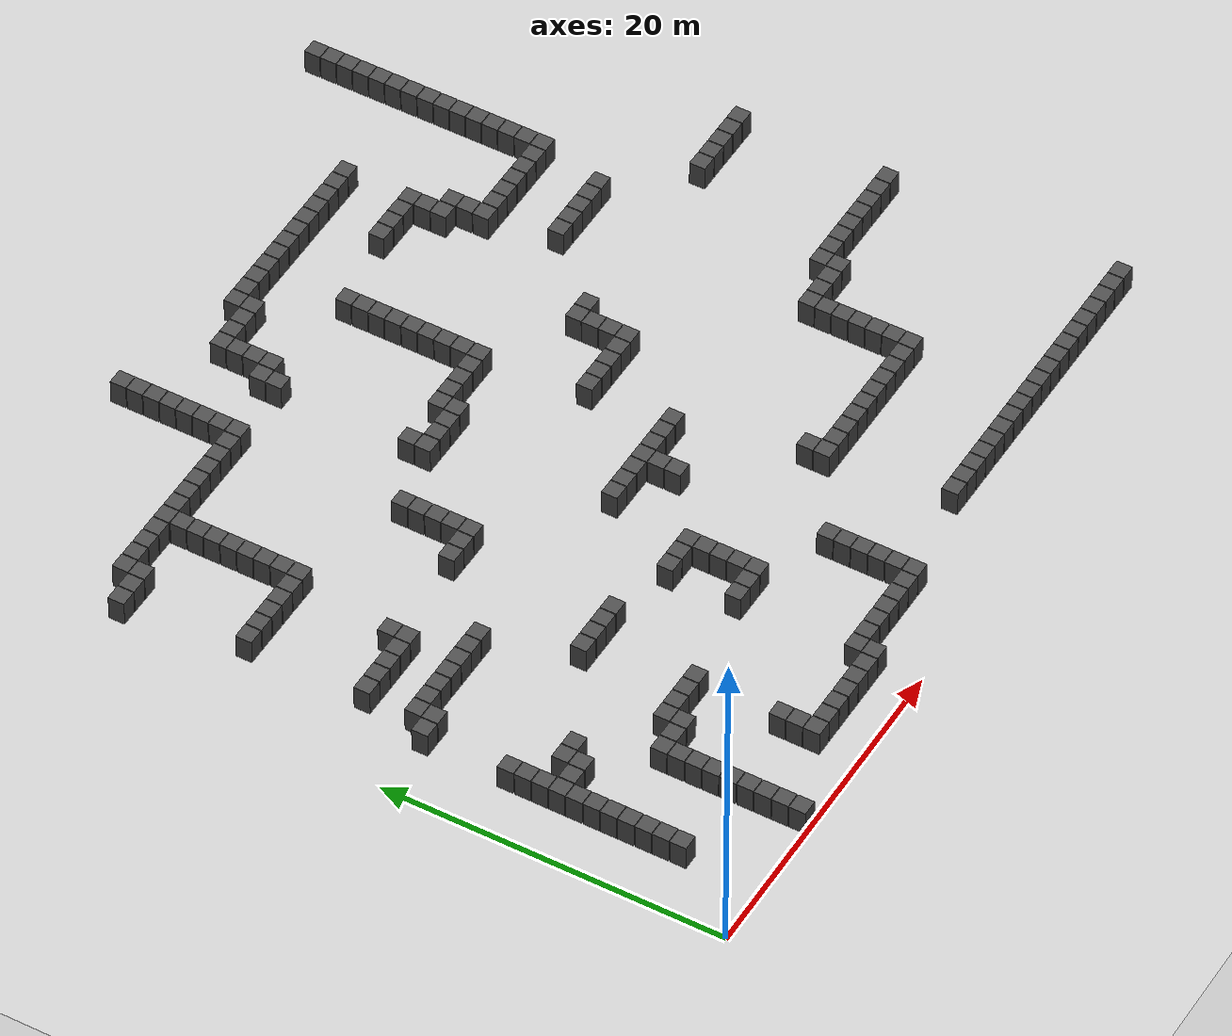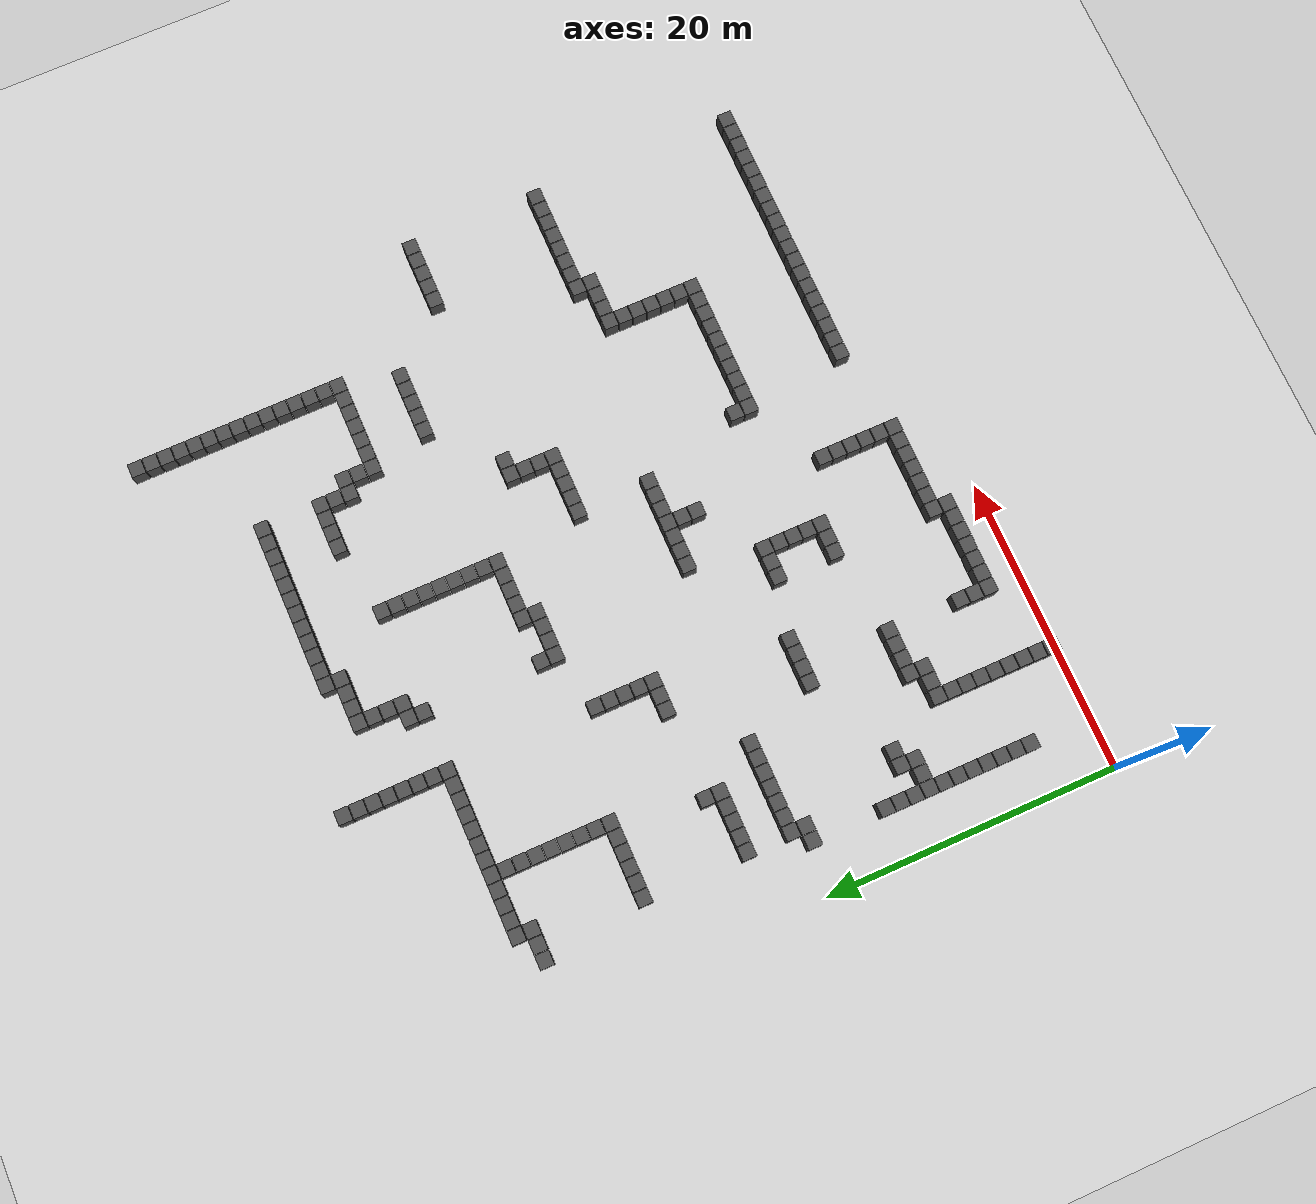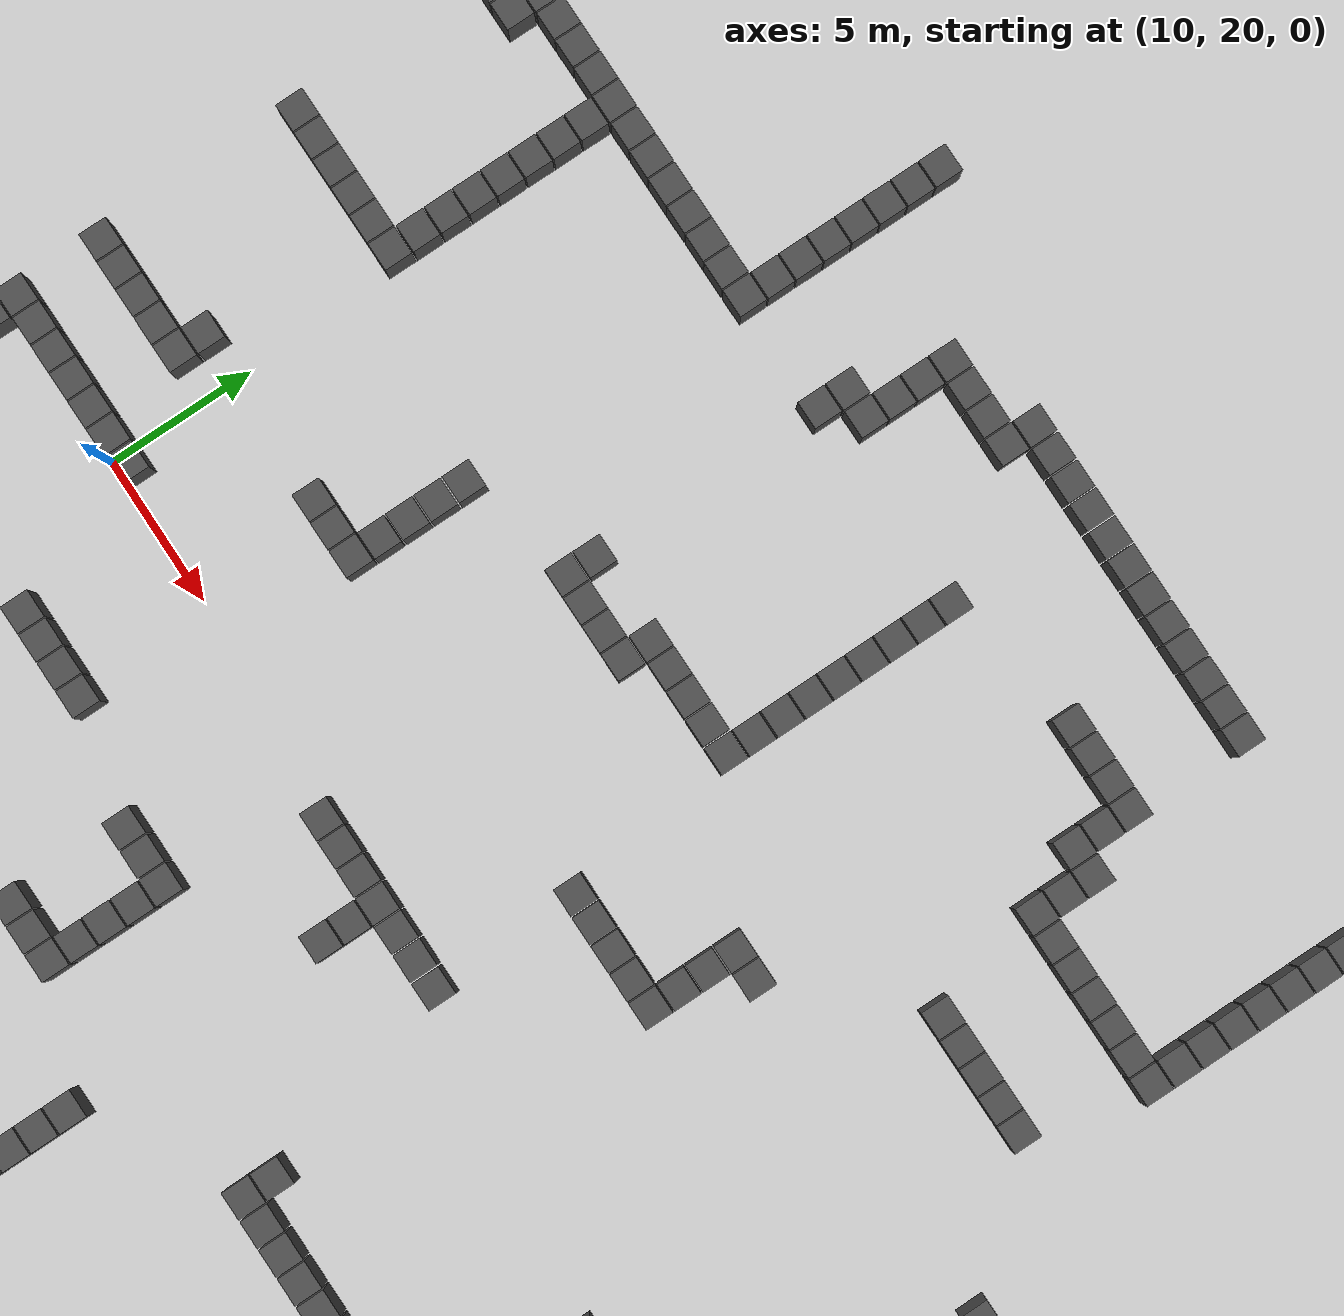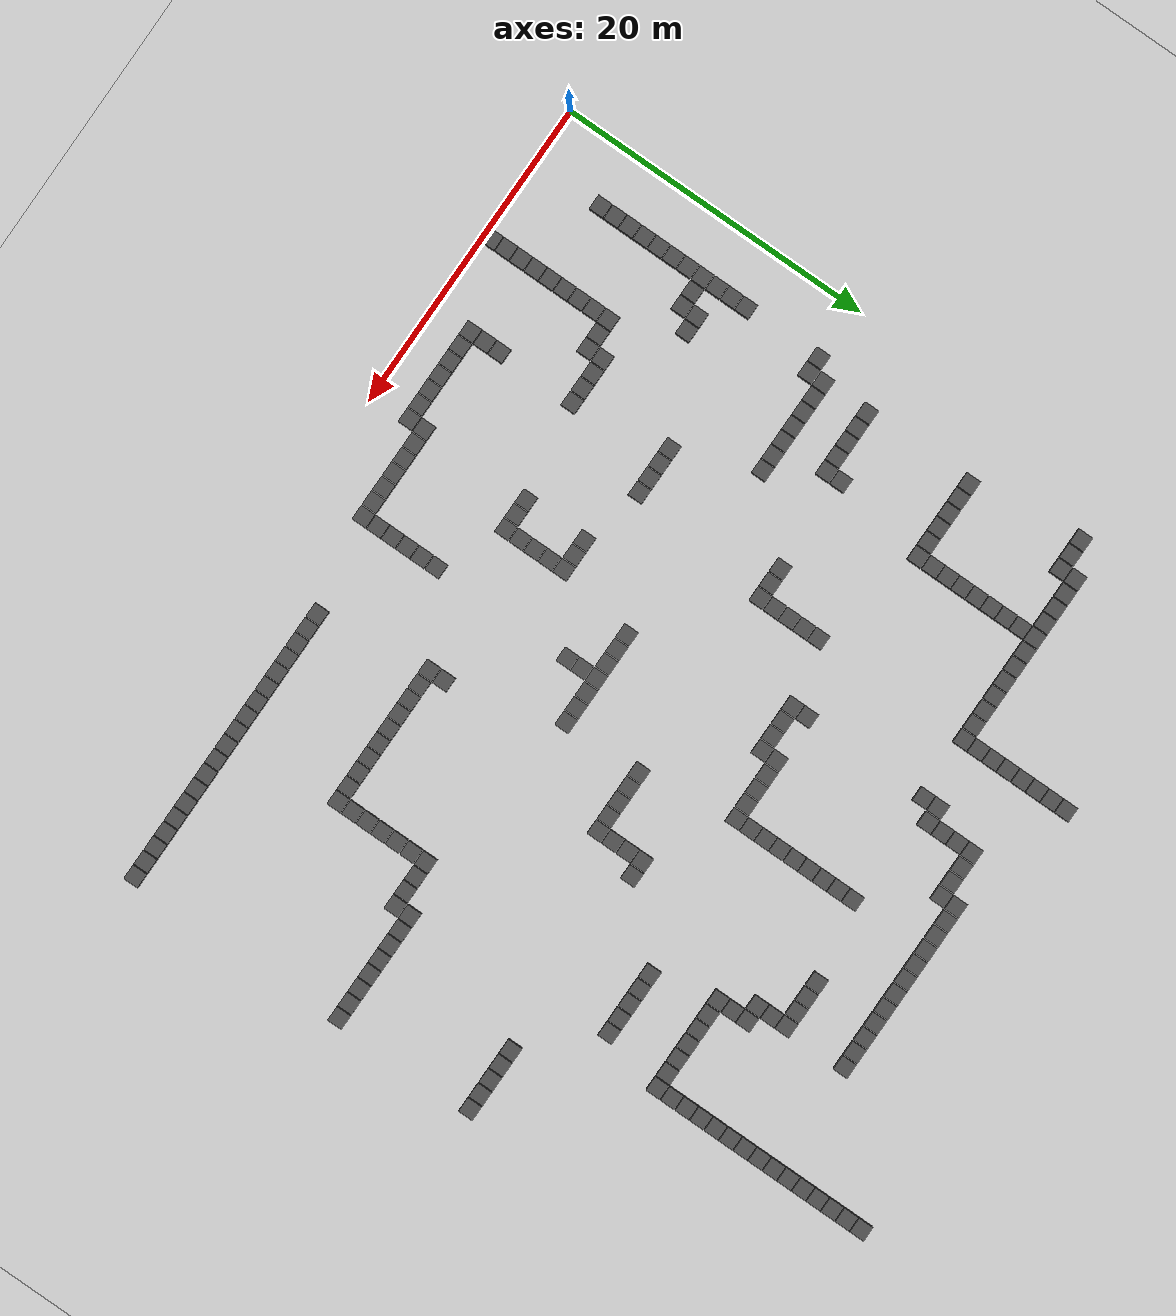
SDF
<?xml version="1.0" ?>
<sdf version="1.6">
  <world name="maze_world">

    <!-- 光源 -->
    <light name="sun" type="directional">
      <cast_shadows>true</cast_shadows>
      <pose>0 0 10 0 0 0</pose>
      <diffuse>0.8 0.8 0.8 1</diffuse>
      <specular>0.2 0.2 0.2 1</specular>
      <direction>-0.5 0.1 -0.9</direction>
    </light>

    <!-- 物理引擎 -->
    <physics name="default_physics" default="0" type="ode">
      <real_time_update_rate>1000.0</real_time_update_rate>
      <max_step_size>0.001</max_step_size>
    </physics>

    <!-- 地面（覆盖整个地图范围） -->
    <model name="ground_plane">
      <static>true</static>
      <pose>25.0 25.0 0 0 0 0</pose>
      <link name="link">
        <collision name="collision">
          <geometry>
            <plane>
              <normal>0 0 1</normal>
              <size>50.0 50.0</size>
            </plane>
          </geometry>
        </collision>
        <visual name="visual">
          <geometry>
            <plane>
              <normal>0 0 1</normal>
              <size>50.0 50.0</size>
            </plane>
          </geometry>
          <material>
            <ambient>0.8 0.8 0.8 1</ambient>
            <diffuse>0.8 0.8 0.8 1</diffuse>
          </material>
        </visual>
      </link>
    </model>

    <!-- 障碍物方块（共 264 个，由 map_maze.png 生成） -->

    <model name="wall_0">
      <static>true</static>
      <pose>42.500 49.500 0.750 0 0 0</pose>
      <link name="link">
        <collision name="collision">
          <geometry>
            <box><size>0.950 0.950 1.500</size></box>
          </geometry>
        </collision>
        <visual name="visual">
          <geometry>
            <box><size>0.950 0.950 1.500</size></box>
          </geometry>
          <material>
            <ambient>0.2 0.2 0.2 1</ambient>
            <diffuse>0.3 0.3 0.3 1</diffuse>
          </material>
        </visual>
      </link>
    </model>

    <model name="wall_1">
      <static>true</static>
      <pose>42.500 48.500 0.750 0 0 0</pose>
      <link name="link">
        <collision name="collision">
          <geometry>
            <box><size>0.950 0.950 1.500</size></box>
          </geometry>
        </collision>
        <visual name="visual">
          <geometry>
            <box><size>0.950 0.950 1.500</size></box>
          </geometry>
          <material>
            <ambient>0.2 0.2 0.2 1</ambient>
            <diffuse>0.3 0.3 0.3 1</diffuse>
          </material>
        </visual>
      </link>
    </model>

    <model name="wall_2">
      <static>true</static>
      <pose>42.500 47.500 0.750 0 0 0</pose>
      <link name="link">
        <collision name="collision">
          <geometry>
            <box><size>0.950 0.950 1.500</size></box>
          </geometry>
        </collision>
        <visual name="visual">
          <geometry>
            <box><size>0.950 0.950 1.500</size></box>
          </geometry>
          <material>
            <ambient>0.2 0.2 0.2 1</ambient>
            <diffuse>0.3 0.3 0.3 1</diffuse>
          </material>
        </visual>
      </link>
    </model>

    <model name="wall_3">
      <static>true</static>
      <pose>42.500 46.500 0.750 0 0 0</pose>
      <link name="link">
        <collision name="collision">
          <geometry>
            <box><size>0.950 0.950 1.500</size></box>
          </geometry>
        </collision>
        <visual name="visual">
          <geometry>
            <box><size>0.950 0.950 1.500</size></box>
          </geometry>
          <material>
            <ambient>0.2 0.2 0.2 1</ambient>
            <diffuse>0.3 0.3 0.3 1</diffuse>
          </material>
        </visual>
      </link>
    </model>

    <model name="wall_4">
      <static>true</static>
      <pose>16.500 45.500 0.750 0 0 0</pose>
      <link name="link">
        <collision name="collision">
          <geometry>
            <box><size>0.950 0.950 1.500</size></box>
          </geometry>
        </collision>
        <visual name="visual">
          <geometry>
            <box><size>0.950 0.950 1.500</size></box>
          </geometry>
          <material>
            <ambient>0.2 0.2 0.2 1</ambient>
            <diffuse>0.3 0.3 0.3 1</diffuse>
          </material>
        </visual>
      </link>
    </model>

    <model name="wall_5">
      <static>true</static>
      <pose>42.500 45.500 0.750 0 0 0</pose>
      <link name="link">
        <collision name="collision">
          <geometry>
            <box><size>0.950 0.950 1.500</size></box>
          </geometry>
        </collision>
        <visual name="visual">
          <geometry>
            <box><size>0.950 0.950 1.500</size></box>
          </geometry>
          <material>
            <ambient>0.2 0.2 0.2 1</ambient>
            <diffuse>0.3 0.3 0.3 1</diffuse>
          </material>
        </visual>
      </link>
    </model>

    <model name="wall_6">
      <static>true</static>
      <pose>16.500 44.500 0.750 0 0 0</pose>
      <link name="link">
        <collision name="collision">
          <geometry>
            <box><size>0.950 0.950 1.500</size></box>
          </geometry>
        </collision>
        <visual name="visual">
          <geometry>
            <box><size>0.950 0.950 1.500</size></box>
          </geometry>
          <material>
            <ambient>0.2 0.2 0.2 1</ambient>
            <diffuse>0.3 0.3 0.3 1</diffuse>
          </material>
        </visual>
      </link>
    </model>

    <model name="wall_7">
      <static>true</static>
      <pose>42.500 44.500 0.750 0 0 0</pose>
      <link name="link">
        <collision name="collision">
          <geometry>
            <box><size>0.950 0.950 1.500</size></box>
          </geometry>
        </collision>
        <visual name="visual">
          <geometry>
            <box><size>0.950 0.950 1.500</size></box>
          </geometry>
          <material>
            <ambient>0.2 0.2 0.2 1</ambient>
            <diffuse>0.3 0.3 0.3 1</diffuse>
          </material>
        </visual>
      </link>
    </model>

    <model name="wall_8">
      <static>true</static>
      <pose>16.500 43.500 0.750 0 0 0</pose>
      <link name="link">
        <collision name="collision">
          <geometry>
            <box><size>0.950 0.950 1.500</size></box>
          </geometry>
        </collision>
        <visual name="visual">
          <geometry>
            <box><size>0.950 0.950 1.500</size></box>
          </geometry>
          <material>
            <ambient>0.2 0.2 0.2 1</ambient>
            <diffuse>0.3 0.3 0.3 1</diffuse>
          </material>
        </visual>
      </link>
    </model>

    <model name="wall_9">
      <static>true</static>
      <pose>24.500 43.500 0.750 0 0 0</pose>
      <link name="link">
        <collision name="collision">
          <geometry>
            <box><size>0.950 0.950 1.500</size></box>
          </geometry>
        </collision>
        <visual name="visual">
          <geometry>
            <box><size>0.950 0.950 1.500</size></box>
          </geometry>
          <material>
            <ambient>0.2 0.2 0.2 1</ambient>
            <diffuse>0.3 0.3 0.3 1</diffuse>
          </material>
        </visual>
      </link>
    </model>

    <model name="wall_10">
      <static>true</static>
      <pose>25.500 43.500 0.750 0 0 0</pose>
      <link name="link">
        <collision name="collision">
          <geometry>
            <box><size>0.950 0.950 1.500</size></box>
          </geometry>
        </collision>
        <visual name="visual">
          <geometry>
            <box><size>0.950 0.950 1.500</size></box>
          </geometry>
          <material>
            <ambient>0.2 0.2 0.2 1</ambient>
            <diffuse>0.3 0.3 0.3 1</diffuse>
          </material>
        </visual>
      </link>
    </model>

    <model name="wall_11">
      <static>true</static>
      <pose>26.500 43.500 0.750 0 0 0</pose>
      <link name="link">
        <collision name="collision">
          <geometry>
            <box><size>0.950 0.950 1.500</size></box>
          </geometry>
        </collision>
        <visual name="visual">
          <geometry>
            <box><size>0.950 0.950 1.500</size></box>
          </geometry>
          <material>
            <ambient>0.2 0.2 0.2 1</ambient>
            <diffuse>0.3 0.3 0.3 1</diffuse>
          </material>
        </visual>
      </link>
    </model>

    <model name="wall_12">
      <static>true</static>
      <pose>27.500 43.500 0.750 0 0 0</pose>
      <link name="link">
        <collision name="collision">
          <geometry>
            <box><size>0.950 0.950 1.500</size></box>
          </geometry>
        </collision>
        <visual name="visual">
          <geometry>
            <box><size>0.950 0.950 1.500</size></box>
          </geometry>
          <material>
            <ambient>0.2 0.2 0.2 1</ambient>
            <diffuse>0.3 0.3 0.3 1</diffuse>
          </material>
        </visual>
      </link>
    </model>

    <model name="wall_13">
      <static>true</static>
      <pose>28.500 43.500 0.750 0 0 0</pose>
      <link name="link">
        <collision name="collision">
          <geometry>
            <box><size>0.950 0.950 1.500</size></box>
          </geometry>
        </collision>
        <visual name="visual">
          <geometry>
            <box><size>0.950 0.950 1.500</size></box>
          </geometry>
          <material>
            <ambient>0.2 0.2 0.2 1</ambient>
            <diffuse>0.3 0.3 0.3 1</diffuse>
          </material>
        </visual>
      </link>
    </model>

    <model name="wall_14">
      <static>true</static>
      <pose>29.500 43.500 0.750 0 0 0</pose>
      <link name="link">
        <collision name="collision">
          <geometry>
            <box><size>0.950 0.950 1.500</size></box>
          </geometry>
        </collision>
        <visual name="visual">
          <geometry>
            <box><size>0.950 0.950 1.500</size></box>
          </geometry>
          <material>
            <ambient>0.2 0.2 0.2 1</ambient>
            <diffuse>0.3 0.3 0.3 1</diffuse>
          </material>
        </visual>
      </link>
    </model>

    <model name="wall_15">
      <static>true</static>
      <pose>30.500 43.500 0.750 0 0 0</pose>
      <link name="link">
        <collision name="collision">
          <geometry>
            <box><size>0.950 0.950 1.500</size></box>
          </geometry>
        </collision>
        <visual name="visual">
          <geometry>
            <box><size>0.950 0.950 1.500</size></box>
          </geometry>
          <material>
            <ambient>0.2 0.2 0.2 1</ambient>
            <diffuse>0.3 0.3 0.3 1</diffuse>
          </material>
        </visual>
      </link>
    </model>

    <model name="wall_16">
      <static>true</static>
      <pose>31.500 43.500 0.750 0 0 0</pose>
      <link name="link">
        <collision name="collision">
          <geometry>
            <box><size>0.950 0.950 1.500</size></box>
          </geometry>
        </collision>
        <visual name="visual">
          <geometry>
            <box><size>0.950 0.950 1.500</size></box>
          </geometry>
          <material>
            <ambient>0.2 0.2 0.2 1</ambient>
            <diffuse>0.3 0.3 0.3 1</diffuse>
          </material>
        </visual>
      </link>
    </model>

    <model name="wall_17">
      <static>true</static>
      <pose>32.500 43.500 0.750 0 0 0</pose>
      <link name="link">
        <collision name="collision">
          <geometry>
            <box><size>0.950 0.950 1.500</size></box>
          </geometry>
        </collision>
        <visual name="visual">
          <geometry>
            <box><size>0.950 0.950 1.500</size></box>
          </geometry>
          <material>
            <ambient>0.2 0.2 0.2 1</ambient>
            <diffuse>0.3 0.3 0.3 1</diffuse>
          </material>
        </visual>
      </link>
    </model>

    <model name="wall_18">
      <static>true</static>
      <pose>33.500 43.500 0.750 0 0 0</pose>
      <link name="link">
        <collision name="collision">
          <geometry>
            <box><size>0.950 0.950 1.500</size></box>
          </geometry>
        </collision>
        <visual name="visual">
          <geometry>
            <box><size>0.950 0.950 1.500</size></box>
          </geometry>
          <material>
            <ambient>0.2 0.2 0.2 1</ambient>
            <diffuse>0.3 0.3 0.3 1</diffuse>
          </material>
        </visual>
      </link>
    </model>

    <model name="wall_19">
      <static>true</static>
      <pose>34.500 43.500 0.750 0 0 0</pose>
      <link name="link">
        <collision name="collision">
          <geometry>
            <box><size>0.950 0.950 1.500</size></box>
          </geometry>
        </collision>
        <visual name="visual">
          <geometry>
            <box><size>0.950 0.950 1.500</size></box>
          </geometry>
          <material>
            <ambient>0.2 0.2 0.2 1</ambient>
            <diffuse>0.3 0.3 0.3 1</diffuse>
          </material>
        </visual>
      </link>
    </model>

    <model name="wall_20">
      <static>true</static>
      <pose>35.500 43.500 0.750 0 0 0</pose>
      <link name="link">
        <collision name="collision">
          <geometry>
            <box><size>0.950 0.950 1.500</size></box>
          </geometry>
        </collision>
        <visual name="visual">
          <geometry>
            <box><size>0.950 0.950 1.500</size></box>
          </geometry>
          <material>
            <ambient>0.2 0.2 0.2 1</ambient>
            <diffuse>0.3 0.3 0.3 1</diffuse>
          </material>
        </visual>
      </link>
    </model>

    <model name="wall_21">
      <static>true</static>
      <pose>42.500 43.500 0.750 0 0 0</pose>
      <link name="link">
        <collision name="collision">
          <geometry>
            <box><size>0.950 0.950 1.500</size></box>
          </geometry>
        </collision>
        <visual name="visual">
          <geometry>
            <box><size>0.950 0.950 1.500</size></box>
          </geometry>
          <material>
            <ambient>0.2 0.2 0.2 1</ambient>
            <diffuse>0.3 0.3 0.3 1</diffuse>
          </material>
        </visual>
      </link>
    </model>

    <model name="wall_22">
      <static>true</static>
      <pose>16.500 42.500 0.750 0 0 0</pose>
      <link name="link">
        <collision name="collision">
          <geometry>
            <box><size>0.950 0.950 1.500</size></box>
          </geometry>
        </collision>
        <visual name="visual">
          <geometry>
            <box><size>0.950 0.950 1.500</size></box>
          </geometry>
          <material>
            <ambient>0.2 0.2 0.2 1</ambient>
            <diffuse>0.3 0.3 0.3 1</diffuse>
          </material>
        </visual>
      </link>
    </model>

    <model name="wall_23">
      <static>true</static>
      <pose>21.500 42.500 0.750 0 0 0</pose>
      <link name="link">
        <collision name="collision">
          <geometry>
            <box><size>0.950 0.950 1.500</size></box>
          </geometry>
        </collision>
        <visual name="visual">
          <geometry>
            <box><size>0.950 0.950 1.500</size></box>
          </geometry>
          <material>
            <ambient>0.2 0.2 0.2 1</ambient>
            <diffuse>0.3 0.3 0.3 1</diffuse>
          </material>
        </visual>
      </link>
    </model>

    <model name="wall_24">
      <static>true</static>
      <pose>22.500 42.500 0.750 0 0 0</pose>
      <link name="link">
        <collision name="collision">
          <geometry>
            <box><size>0.950 0.950 1.500</size></box>
          </geometry>
        </collision>
        <visual name="visual">
          <geometry>
            <box><size>0.950 0.950 1.500</size></box>
          </geometry>
          <material>
            <ambient>0.2 0.2 0.2 1</ambient>
            <diffuse>0.3 0.3 0.3 1</diffuse>
          </material>
        </visual>
      </link>
    </model>

    <model name="wall_25">
      <static>true</static>
      <pose>23.500 42.500 0.750 0 0 0</pose>
      <link name="link">
        <collision name="collision">
          <geometry>
            <box><size>0.950 0.950 1.500</size></box>
          </geometry>
        </collision>
        <visual name="visual">
          <geometry>
            <box><size>0.950 0.950 1.500</size></box>
          </geometry>
          <material>
            <ambient>0.2 0.2 0.2 1</ambient>
            <diffuse>0.3 0.3 0.3 1</diffuse>
          </material>
        </visual>
      </link>
    </model>

    <model name="wall_26">
      <static>true</static>
      <pose>24.500 42.500 0.750 0 0 0</pose>
      <link name="link">
        <collision name="collision">
          <geometry>
            <box><size>0.950 0.950 1.500</size></box>
          </geometry>
        </collision>
        <visual name="visual">
          <geometry>
            <box><size>0.950 0.950 1.500</size></box>
          </geometry>
          <material>
            <ambient>0.2 0.2 0.2 1</ambient>
            <diffuse>0.3 0.3 0.3 1</diffuse>
          </material>
        </visual>
      </link>
    </model>

    <model name="wall_27">
      <static>true</static>
      <pose>42.500 42.500 0.750 0 0 0</pose>
      <link name="link">
        <collision name="collision">
          <geometry>
            <box><size>0.950 0.950 1.500</size></box>
          </geometry>
        </collision>
        <visual name="visual">
          <geometry>
            <box><size>0.950 0.950 1.500</size></box>
          </geometry>
          <material>
            <ambient>0.2 0.2 0.2 1</ambient>
            <diffuse>0.3 0.3 0.3 1</diffuse>
          </material>
        </visual>
      </link>
    </model>

    <model name="wall_28">
      <static>true</static>
      <pose>16.500 41.500 0.750 0 0 0</pose>
      <link name="link">
        <collision name="collision">
          <geometry>
            <box><size>0.950 0.950 1.500</size></box>
          </geometry>
        </collision>
        <visual name="visual">
          <geometry>
            <box><size>0.950 0.950 1.500</size></box>
          </geometry>
          <material>
            <ambient>0.2 0.2 0.2 1</ambient>
            <diffuse>0.3 0.3 0.3 1</diffuse>
          </material>
        </visual>
      </link>
    </model>

    <model name="wall_29">
      <static>true</static>
      <pose>21.500 41.500 0.750 0 0 0</pose>
      <link name="link">
        <collision name="collision">
          <geometry>
            <box><size>0.950 0.950 1.500</size></box>
          </geometry>
        </collision>
        <visual name="visual">
          <geometry>
            <box><size>0.950 0.950 1.500</size></box>
          </geometry>
          <material>
            <ambient>0.2 0.2 0.2 1</ambient>
            <diffuse>0.3 0.3 0.3 1</diffuse>
          </material>
        </visual>
      </link>
    </model>

    <model name="wall_30">
      <static>true</static>
      <pose>42.500 41.500 0.750 0 0 0</pose>
      <link name="link">
        <collision name="collision">
          <geometry>
            <box><size>0.950 0.950 1.500</size></box>
          </geometry>
        </collision>
        <visual name="visual">
          <geometry>
            <box><size>0.950 0.950 1.500</size></box>
          </geometry>
          <material>
            <ambient>0.2 0.2 0.2 1</ambient>
            <diffuse>0.3 0.3 0.3 1</diffuse>
          </material>
        </visual>
      </link>
    </model>

    <model name="wall_31">
      <static>true</static>
      <pose>16.500 40.500 0.750 0 0 0</pose>
      <link name="link">
        <collision name="collision">
          <geometry>
            <box><size>0.950 0.950 1.500</size></box>
          </geometry>
        </collision>
        <visual name="visual">
          <geometry>
            <box><size>0.950 0.950 1.500</size></box>
          </geometry>
          <material>
            <ambient>0.2 0.2 0.2 1</ambient>
            <diffuse>0.3 0.3 0.3 1</diffuse>
          </material>
        </visual>
      </link>
    </model>

    <model name="wall_32">
      <static>true</static>
      <pose>21.500 40.500 0.750 0 0 0</pose>
      <link name="link">
        <collision name="collision">
          <geometry>
            <box><size>0.950 0.950 1.500</size></box>
          </geometry>
        </collision>
        <visual name="visual">
          <geometry>
            <box><size>0.950 0.950 1.500</size></box>
          </geometry>
          <material>
            <ambient>0.2 0.2 0.2 1</ambient>
            <diffuse>0.3 0.3 0.3 1</diffuse>
          </material>
        </visual>
      </link>
    </model>

    <model name="wall_33">
      <static>true</static>
      <pose>42.500 40.500 0.750 0 0 0</pose>
      <link name="link">
        <collision name="collision">
          <geometry>
            <box><size>0.950 0.950 1.500</size></box>
          </geometry>
        </collision>
        <visual name="visual">
          <geometry>
            <box><size>0.950 0.950 1.500</size></box>
          </geometry>
          <material>
            <ambient>0.2 0.2 0.2 1</ambient>
            <diffuse>0.3 0.3 0.3 1</diffuse>
          </material>
        </visual>
      </link>
    </model>

    <model name="wall_34">
      <static>true</static>
      <pose>16.500 39.500 0.750 0 0 0</pose>
      <link name="link">
        <collision name="collision">
          <geometry>
            <box><size>0.950 0.950 1.500</size></box>
          </geometry>
        </collision>
        <visual name="visual">
          <geometry>
            <box><size>0.950 0.950 1.500</size></box>
          </geometry>
          <material>
            <ambient>0.2 0.2 0.2 1</ambient>
            <diffuse>0.3 0.3 0.3 1</diffuse>
          </material>
        </visual>
      </link>
    </model>

    <model name="wall_35">
      <static>true</static>
      <pose>20.500 39.500 0.750 0 0 0</pose>
      <link name="link">
        <collision name="collision">
          <geometry>
            <box><size>0.950 0.950 1.500</size></box>
          </geometry>
        </collision>
        <visual name="visual">
          <geometry>
            <box><size>0.950 0.950 1.500</size></box>
          </geometry>
          <material>
            <ambient>0.2 0.2 0.2 1</ambient>
            <diffuse>0.3 0.3 0.3 1</diffuse>
          </material>
        </visual>
      </link>
    </model>

    <model name="wall_36">
      <static>true</static>
      <pose>21.500 39.500 0.750 0 0 0</pose>
      <link name="link">
        <collision name="collision">
          <geometry>
            <box><size>0.950 0.950 1.500</size></box>
          </geometry>
        </collision>
        <visual name="visual">
          <geometry>
            <box><size>0.950 0.950 1.500</size></box>
          </geometry>
          <material>
            <ambient>0.2 0.2 0.2 1</ambient>
            <diffuse>0.3 0.3 0.3 1</diffuse>
          </material>
        </visual>
      </link>
    </model>

    <model name="wall_37">
      <static>true</static>
      <pose>32.500 39.500 0.750 0 0 0</pose>
      <link name="link">
        <collision name="collision">
          <geometry>
            <box><size>0.950 0.950 1.500</size></box>
          </geometry>
        </collision>
        <visual name="visual">
          <geometry>
            <box><size>0.950 0.950 1.500</size></box>
          </geometry>
          <material>
            <ambient>0.2 0.2 0.2 1</ambient>
            <diffuse>0.3 0.3 0.3 1</diffuse>
          </material>
        </visual>
      </link>
    </model>

    <model name="wall_38">
      <static>true</static>
      <pose>33.500 39.500 0.750 0 0 0</pose>
      <link name="link">
        <collision name="collision">
          <geometry>
            <box><size>0.950 0.950 1.500</size></box>
          </geometry>
        </collision>
        <visual name="visual">
          <geometry>
            <box><size>0.950 0.950 1.500</size></box>
          </geometry>
          <material>
            <ambient>0.2 0.2 0.2 1</ambient>
            <diffuse>0.3 0.3 0.3 1</diffuse>
          </material>
        </visual>
      </link>
    </model>

    <model name="wall_39">
      <static>true</static>
      <pose>34.500 39.500 0.750 0 0 0</pose>
      <link name="link">
        <collision name="collision">
          <geometry>
            <box><size>0.950 0.950 1.500</size></box>
          </geometry>
        </collision>
        <visual name="visual">
          <geometry>
            <box><size>0.950 0.950 1.500</size></box>
          </geometry>
          <material>
            <ambient>0.2 0.2 0.2 1</ambient>
            <diffuse>0.3 0.3 0.3 1</diffuse>
          </material>
        </visual>
      </link>
    </model>

    <model name="wall_40">
      <static>true</static>
      <pose>35.500 39.500 0.750 0 0 0</pose>
      <link name="link">
        <collision name="collision">
          <geometry>
            <box><size>0.950 0.950 1.500</size></box>
          </geometry>
        </collision>
        <visual name="visual">
          <geometry>
            <box><size>0.950 0.950 1.500</size></box>
          </geometry>
          <material>
            <ambient>0.2 0.2 0.2 1</ambient>
            <diffuse>0.3 0.3 0.3 1</diffuse>
          </material>
        </visual>
      </link>
    </model>

    <model name="wall_41">
      <static>true</static>
      <pose>42.500 39.500 0.750 0 0 0</pose>
      <link name="link">
        <collision name="collision">
          <geometry>
            <box><size>0.950 0.950 1.500</size></box>
          </geometry>
        </collision>
        <visual name="visual">
          <geometry>
            <box><size>0.950 0.950 1.500</size></box>
          </geometry>
          <material>
            <ambient>0.2 0.2 0.2 1</ambient>
            <diffuse>0.3 0.3 0.3 1</diffuse>
          </material>
        </visual>
      </link>
    </model>

    <model name="wall_42">
      <static>true</static>
      <pose>5.500 38.500 0.750 0 0 0</pose>
      <link name="link">
        <collision name="collision">
          <geometry>
            <box><size>0.950 0.950 1.500</size></box>
          </geometry>
        </collision>
        <visual name="visual">
          <geometry>
            <box><size>0.950 0.950 1.500</size></box>
          </geometry>
          <material>
            <ambient>0.2 0.2 0.2 1</ambient>
            <diffuse>0.3 0.3 0.3 1</diffuse>
          </material>
        </visual>
      </link>
    </model>

    <model name="wall_43">
      <static>true</static>
      <pose>6.500 38.500 0.750 0 0 0</pose>
      <link name="link">
        <collision name="collision">
          <geometry>
            <box><size>0.950 0.950 1.500</size></box>
          </geometry>
        </collision>
        <visual name="visual">
          <geometry>
            <box><size>0.950 0.950 1.500</size></box>
          </geometry>
          <material>
            <ambient>0.2 0.2 0.2 1</ambient>
            <diffuse>0.3 0.3 0.3 1</diffuse>
          </material>
        </visual>
      </link>
    </model>

    <model name="wall_44">
      <static>true</static>
      <pose>7.500 38.500 0.750 0 0 0</pose>
      <link name="link">
        <collision name="collision">
          <geometry>
            <box><size>0.950 0.950 1.500</size></box>
          </geometry>
        </collision>
        <visual name="visual">
          <geometry>
            <box><size>0.950 0.950 1.500</size></box>
          </geometry>
          <material>
            <ambient>0.2 0.2 0.2 1</ambient>
            <diffuse>0.3 0.3 0.3 1</diffuse>
          </material>
        </visual>
      </link>
    </model>

    <model name="wall_45">
      <static>true</static>
      <pose>8.500 38.500 0.750 0 0 0</pose>
      <link name="link">
        <collision name="collision">
          <geometry>
            <box><size>0.950 0.950 1.500</size></box>
          </geometry>
        </collision>
        <visual name="visual">
          <geometry>
            <box><size>0.950 0.950 1.500</size></box>
          </geometry>
          <material>
            <ambient>0.2 0.2 0.2 1</ambient>
            <diffuse>0.3 0.3 0.3 1</diffuse>
          </material>
        </visual>
      </link>
    </model>

    <model name="wall_46">
      <static>true</static>
      <pose>9.500 38.500 0.750 0 0 0</pose>
      <link name="link">
        <collision name="collision">
          <geometry>
            <box><size>0.950 0.950 1.500</size></box>
          </geometry>
        </collision>
        <visual name="visual">
          <geometry>
            <box><size>0.950 0.950 1.500</size></box>
          </geometry>
          <material>
            <ambient>0.2 0.2 0.2 1</ambient>
            <diffuse>0.3 0.3 0.3 1</diffuse>
          </material>
        </visual>
      </link>
    </model>

    <model name="wall_47">
      <static>true</static>
      <pose>10.500 38.500 0.750 0 0 0</pose>
      <link name="link">
        <collision name="collision">
          <geometry>
            <box><size>0.950 0.950 1.500</size></box>
          </geometry>
        </collision>
        <visual name="visual">
          <geometry>
            <box><size>0.950 0.950 1.500</size></box>
          </geometry>
          <material>
            <ambient>0.2 0.2 0.2 1</ambient>
            <diffuse>0.3 0.3 0.3 1</diffuse>
          </material>
        </visual>
      </link>
    </model>

    <model name="wall_48">
      <static>true</static>
      <pose>11.500 38.500 0.750 0 0 0</pose>
      <link name="link">
        <collision name="collision">
          <geometry>
            <box><size>0.950 0.950 1.500</size></box>
          </geometry>
        </collision>
        <visual name="visual">
          <geometry>
            <box><size>0.950 0.950 1.500</size></box>
          </geometry>
          <material>
            <ambient>0.2 0.2 0.2 1</ambient>
            <diffuse>0.3 0.3 0.3 1</diffuse>
          </material>
        </visual>
      </link>
    </model>

    <model name="wall_49">
      <static>true</static>
      <pose>12.500 38.500 0.750 0 0 0</pose>
      <link name="link">
        <collision name="collision">
          <geometry>
            <box><size>0.950 0.950 1.500</size></box>
          </geometry>
        </collision>
        <visual name="visual">
          <geometry>
            <box><size>0.950 0.950 1.500</size></box>
          </geometry>
          <material>
            <ambient>0.2 0.2 0.2 1</ambient>
            <diffuse>0.3 0.3 0.3 1</diffuse>
          </material>
        </visual>
      </link>
    </model>

    <model name="wall_50">
      <static>true</static>
      <pose>13.500 38.500 0.750 0 0 0</pose>
      <link name="link">
        <collision name="collision">
          <geometry>
            <box><size>0.950 0.950 1.500</size></box>
          </geometry>
        </collision>
        <visual name="visual">
          <geometry>
            <box><size>0.950 0.950 1.500</size></box>
          </geometry>
          <material>
            <ambient>0.2 0.2 0.2 1</ambient>
            <diffuse>0.3 0.3 0.3 1</diffuse>
          </material>
        </visual>
      </link>
    </model>

    <model name="wall_51">
      <static>true</static>
      <pose>14.500 38.500 0.750 0 0 0</pose>
      <link name="link">
        <collision name="collision">
          <geometry>
            <box><size>0.950 0.950 1.500</size></box>
          </geometry>
        </collision>
        <visual name="visual">
          <geometry>
            <box><size>0.950 0.950 1.500</size></box>
          </geometry>
          <material>
            <ambient>0.2 0.2 0.2 1</ambient>
            <diffuse>0.3 0.3 0.3 1</diffuse>
          </material>
        </visual>
      </link>
    </model>

    <model name="wall_52">
      <static>true</static>
      <pose>15.500 38.500 0.750 0 0 0</pose>
      <link name="link">
        <collision name="collision">
          <geometry>
            <box><size>0.950 0.950 1.500</size></box>
          </geometry>
        </collision>
        <visual name="visual">
          <geometry>
            <box><size>0.950 0.950 1.500</size></box>
          </geometry>
          <material>
            <ambient>0.2 0.2 0.2 1</ambient>
            <diffuse>0.3 0.3 0.3 1</diffuse>
          </material>
        </visual>
      </link>
    </model>

    <model name="wall_53">
      <static>true</static>
      <pose>16.500 38.500 0.750 0 0 0</pose>
      <link name="link">
        <collision name="collision">
          <geometry>
            <box><size>0.950 0.950 1.500</size></box>
          </geometry>
        </collision>
        <visual name="visual">
          <geometry>
            <box><size>0.950 0.950 1.500</size></box>
          </geometry>
          <material>
            <ambient>0.2 0.2 0.2 1</ambient>
            <diffuse>0.3 0.3 0.3 1</diffuse>
          </material>
        </visual>
      </link>
    </model>

    <model name="wall_54">
      <static>true</static>
      <pose>20.500 38.500 0.750 0 0 0</pose>
      <link name="link">
        <collision name="collision">
          <geometry>
            <box><size>0.950 0.950 1.500</size></box>
          </geometry>
        </collision>
        <visual name="visual">
          <geometry>
            <box><size>0.950 0.950 1.500</size></box>
          </geometry>
          <material>
            <ambient>0.2 0.2 0.2 1</ambient>
            <diffuse>0.3 0.3 0.3 1</diffuse>
          </material>
        </visual>
      </link>
    </model>

    <model name="wall_55">
      <static>true</static>
      <pose>27.500 38.500 0.750 0 0 0</pose>
      <link name="link">
        <collision name="collision">
          <geometry>
            <box><size>0.950 0.950 1.500</size></box>
          </geometry>
        </collision>
        <visual name="visual">
          <geometry>
            <box><size>0.950 0.950 1.500</size></box>
          </geometry>
          <material>
            <ambient>0.2 0.2 0.2 1</ambient>
            <diffuse>0.3 0.3 0.3 1</diffuse>
          </material>
        </visual>
      </link>
    </model>

    <model name="wall_56">
      <static>true</static>
      <pose>35.500 38.500 0.750 0 0 0</pose>
      <link name="link">
        <collision name="collision">
          <geometry>
            <box><size>0.950 0.950 1.500</size></box>
          </geometry>
        </collision>
        <visual name="visual">
          <geometry>
            <box><size>0.950 0.950 1.500</size></box>
          </geometry>
          <material>
            <ambient>0.2 0.2 0.2 1</ambient>
            <diffuse>0.3 0.3 0.3 1</diffuse>
          </material>
        </visual>
      </link>
    </model>

    <model name="wall_57">
      <static>true</static>
      <pose>42.500 38.500 0.750 0 0 0</pose>
      <link name="link">
        <collision name="collision">
          <geometry>
            <box><size>0.950 0.950 1.500</size></box>
          </geometry>
        </collision>
        <visual name="visual">
          <geometry>
            <box><size>0.950 0.950 1.500</size></box>
          </geometry>
          <material>
            <ambient>0.2 0.2 0.2 1</ambient>
            <diffuse>0.3 0.3 0.3 1</diffuse>
          </material>
        </visual>
      </link>
    </model>

    <model name="wall_58">
      <static>true</static>
      <pose>3.500 37.500 0.750 0 0 0</pose>
      <link name="link">
        <collision name="collision">
          <geometry>
            <box><size>0.950 0.950 1.500</size></box>
          </geometry>
        </collision>
        <visual name="visual">
          <geometry>
            <box><size>0.950 0.950 1.500</size></box>
          </geometry>
          <material>
            <ambient>0.2 0.2 0.2 1</ambient>
            <diffuse>0.3 0.3 0.3 1</diffuse>
          </material>
        </visual>
      </link>
    </model>

    <model name="wall_59">
      <static>true</static>
      <pose>4.500 37.500 0.750 0 0 0</pose>
      <link name="link">
        <collision name="collision">
          <geometry>
            <box><size>0.950 0.950 1.500</size></box>
          </geometry>
        </collision>
        <visual name="visual">
          <geometry>
            <box><size>0.950 0.950 1.500</size></box>
          </geometry>
          <material>
            <ambient>0.2 0.2 0.2 1</ambient>
            <diffuse>0.3 0.3 0.3 1</diffuse>
          </material>
        </visual>
      </link>
    </model>

    <model name="wall_60">
      <static>true</static>
      <pose>5.500 37.500 0.750 0 0 0</pose>
      <link name="link">
        <collision name="collision">
          <geometry>
            <box><size>0.950 0.950 1.500</size></box>
          </geometry>
        </collision>
        <visual name="visual">
          <geometry>
            <box><size>0.950 0.950 1.500</size></box>
          </geometry>
          <material>
            <ambient>0.2 0.2 0.2 1</ambient>
            <diffuse>0.3 0.3 0.3 1</diffuse>
          </material>
        </visual>
      </link>
    </model>

    <model name="wall_61">
      <static>true</static>
      <pose>9.500 37.500 0.750 0 0 0</pose>
      <link name="link">
        <collision name="collision">
          <geometry>
            <box><size>0.950 0.950 1.500</size></box>
          </geometry>
        </collision>
        <visual name="visual">
          <geometry>
            <box><size>0.950 0.950 1.500</size></box>
          </geometry>
          <material>
            <ambient>0.2 0.2 0.2 1</ambient>
            <diffuse>0.3 0.3 0.3 1</diffuse>
          </material>
        </visual>
      </link>
    </model>

    <model name="wall_62">
      <static>true</static>
      <pose>27.500 37.500 0.750 0 0 0</pose>
      <link name="link">
        <collision name="collision">
          <geometry>
            <box><size>0.950 0.950 1.500</size></box>
          </geometry>
        </collision>
        <visual name="visual">
          <geometry>
            <box><size>0.950 0.950 1.500</size></box>
          </geometry>
          <material>
            <ambient>0.2 0.2 0.2 1</ambient>
            <diffuse>0.3 0.3 0.3 1</diffuse>
          </material>
        </visual>
      </link>
    </model>

    <model name="wall_63">
      <static>true</static>
      <pose>35.500 37.500 0.750 0 0 0</pose>
      <link name="link">
        <collision name="collision">
          <geometry>
            <box><size>0.950 0.950 1.500</size></box>
          </geometry>
        </collision>
        <visual name="visual">
          <geometry>
            <box><size>0.950 0.950 1.500</size></box>
          </geometry>
          <material>
            <ambient>0.2 0.2 0.2 1</ambient>
            <diffuse>0.3 0.3 0.3 1</diffuse>
          </material>
        </visual>
      </link>
    </model>

    <model name="wall_64">
      <static>true</static>
      <pose>36.500 37.500 0.750 0 0 0</pose>
      <link name="link">
        <collision name="collision">
          <geometry>
            <box><size>0.950 0.950 1.500</size></box>
          </geometry>
        </collision>
        <visual name="visual">
          <geometry>
            <box><size>0.950 0.950 1.500</size></box>
          </geometry>
          <material>
            <ambient>0.2 0.2 0.2 1</ambient>
            <diffuse>0.3 0.3 0.3 1</diffuse>
          </material>
        </visual>
      </link>
    </model>

    <model name="wall_65">
      <static>true</static>
      <pose>42.500 37.500 0.750 0 0 0</pose>
      <link name="link">
        <collision name="collision">
          <geometry>
            <box><size>0.950 0.950 1.500</size></box>
          </geometry>
        </collision>
        <visual name="visual">
          <geometry>
            <box><size>0.950 0.950 1.500</size></box>
          </geometry>
          <material>
            <ambient>0.2 0.2 0.2 1</ambient>
            <diffuse>0.3 0.3 0.3 1</diffuse>
          </material>
        </visual>
      </link>
    </model>

    <model name="wall_66">
      <static>true</static>
      <pose>9.500 36.500 0.750 0 0 0</pose>
      <link name="link">
        <collision name="collision">
          <geometry>
            <box><size>0.950 0.950 1.500</size></box>
          </geometry>
        </collision>
        <visual name="visual">
          <geometry>
            <box><size>0.950 0.950 1.500</size></box>
          </geometry>
          <material>
            <ambient>0.2 0.2 0.2 1</ambient>
            <diffuse>0.3 0.3 0.3 1</diffuse>
          </material>
        </visual>
      </link>
    </model>

    <model name="wall_67">
      <static>true</static>
      <pose>27.500 36.500 0.750 0 0 0</pose>
      <link name="link">
        <collision name="collision">
          <geometry>
            <box><size>0.950 0.950 1.500</size></box>
          </geometry>
        </collision>
        <visual name="visual">
          <geometry>
            <box><size>0.950 0.950 1.500</size></box>
          </geometry>
          <material>
            <ambient>0.2 0.2 0.2 1</ambient>
            <diffuse>0.3 0.3 0.3 1</diffuse>
          </material>
        </visual>
      </link>
    </model>

    <model name="wall_68">
      <static>true</static>
      <pose>36.500 36.500 0.750 0 0 0</pose>
      <link name="link">
        <collision name="collision">
          <geometry>
            <box><size>0.950 0.950 1.500</size></box>
          </geometry>
        </collision>
        <visual name="visual">
          <geometry>
            <box><size>0.950 0.950 1.500</size></box>
          </geometry>
          <material>
            <ambient>0.2 0.2 0.2 1</ambient>
            <diffuse>0.3 0.3 0.3 1</diffuse>
          </material>
        </visual>
      </link>
    </model>

    <model name="wall_69">
      <static>true</static>
      <pose>42.500 36.500 0.750 0 0 0</pose>
      <link name="link">
        <collision name="collision">
          <geometry>
            <box><size>0.950 0.950 1.500</size></box>
          </geometry>
        </collision>
        <visual name="visual">
          <geometry>
            <box><size>0.950 0.950 1.500</size></box>
          </geometry>
          <material>
            <ambient>0.2 0.2 0.2 1</ambient>
            <diffuse>0.3 0.3 0.3 1</diffuse>
          </material>
        </visual>
      </link>
    </model>

    <model name="wall_70">
      <static>true</static>
      <pose>9.500 35.500 0.750 0 0 0</pose>
      <link name="link">
        <collision name="collision">
          <geometry>
            <box><size>0.950 0.950 1.500</size></box>
          </geometry>
        </collision>
        <visual name="visual">
          <geometry>
            <box><size>0.950 0.950 1.500</size></box>
          </geometry>
          <material>
            <ambient>0.2 0.2 0.2 1</ambient>
            <diffuse>0.3 0.3 0.3 1</diffuse>
          </material>
        </visual>
      </link>
    </model>

    <model name="wall_71">
      <static>true</static>
      <pose>27.500 35.500 0.750 0 0 0</pose>
      <link name="link">
        <collision name="collision">
          <geometry>
            <box><size>0.950 0.950 1.500</size></box>
          </geometry>
        </collision>
        <visual name="visual">
          <geometry>
            <box><size>0.950 0.950 1.500</size></box>
          </geometry>
          <material>
            <ambient>0.2 0.2 0.2 1</ambient>
            <diffuse>0.3 0.3 0.3 1</diffuse>
          </material>
        </visual>
      </link>
    </model>

    <model name="wall_72">
      <static>true</static>
      <pose>36.500 35.500 0.750 0 0 0</pose>
      <link name="link">
        <collision name="collision">
          <geometry>
            <box><size>0.950 0.950 1.500</size></box>
          </geometry>
        </collision>
        <visual name="visual">
          <geometry>
            <box><size>0.950 0.950 1.500</size></box>
          </geometry>
          <material>
            <ambient>0.2 0.2 0.2 1</ambient>
            <diffuse>0.3 0.3 0.3 1</diffuse>
          </material>
        </visual>
      </link>
    </model>

    <model name="wall_73">
      <static>true</static>
      <pose>37.500 35.500 0.750 0 0 0</pose>
      <link name="link">
        <collision name="collision">
          <geometry>
            <box><size>0.950 0.950 1.500</size></box>
          </geometry>
        </collision>
        <visual name="visual">
          <geometry>
            <box><size>0.950 0.950 1.500</size></box>
          </geometry>
          <material>
            <ambient>0.2 0.2 0.2 1</ambient>
            <diffuse>0.3 0.3 0.3 1</diffuse>
          </material>
        </visual>
      </link>
    </model>

    <model name="wall_74">
      <static>true</static>
      <pose>38.500 35.500 0.750 0 0 0</pose>
      <link name="link">
        <collision name="collision">
          <geometry>
            <box><size>0.950 0.950 1.500</size></box>
          </geometry>
        </collision>
        <visual name="visual">
          <geometry>
            <box><size>0.950 0.950 1.500</size></box>
          </geometry>
          <material>
            <ambient>0.2 0.2 0.2 1</ambient>
            <diffuse>0.3 0.3 0.3 1</diffuse>
          </material>
        </visual>
      </link>
    </model>

    <model name="wall_75">
      <static>true</static>
      <pose>39.500 35.500 0.750 0 0 0</pose>
      <link name="link">
        <collision name="collision">
          <geometry>
            <box><size>0.950 0.950 1.500</size></box>
          </geometry>
        </collision>
        <visual name="visual">
          <geometry>
            <box><size>0.950 0.950 1.500</size></box>
          </geometry>
          <material>
            <ambient>0.2 0.2 0.2 1</ambient>
            <diffuse>0.3 0.3 0.3 1</diffuse>
          </material>
        </visual>
      </link>
    </model>

    <model name="wall_76">
      <static>true</static>
      <pose>40.500 35.500 0.750 0 0 0</pose>
      <link name="link">
        <collision name="collision">
          <geometry>
            <box><size>0.950 0.950 1.500</size></box>
          </geometry>
        </collision>
        <visual name="visual">
          <geometry>
            <box><size>0.950 0.950 1.500</size></box>
          </geometry>
          <material>
            <ambient>0.2 0.2 0.2 1</ambient>
            <diffuse>0.3 0.3 0.3 1</diffuse>
          </material>
        </visual>
      </link>
    </model>

    <model name="wall_77">
      <static>true</static>
      <pose>41.500 35.500 0.750 0 0 0</pose>
      <link name="link">
        <collision name="collision">
          <geometry>
            <box><size>0.950 0.950 1.500</size></box>
          </geometry>
        </collision>
        <visual name="visual">
          <geometry>
            <box><size>0.950 0.950 1.500</size></box>
          </geometry>
          <material>
            <ambient>0.2 0.2 0.2 1</ambient>
            <diffuse>0.3 0.3 0.3 1</diffuse>
          </material>
        </visual>
      </link>
    </model>

    <model name="wall_78">
      <static>true</static>
      <pose>42.500 35.500 0.750 0 0 0</pose>
      <link name="link">
        <collision name="collision">
          <geometry>
            <box><size>0.950 0.950 1.500</size></box>
          </geometry>
        </collision>
        <visual name="visual">
          <geometry>
            <box><size>0.950 0.950 1.500</size></box>
          </geometry>
          <material>
            <ambient>0.2 0.2 0.2 1</ambient>
            <diffuse>0.3 0.3 0.3 1</diffuse>
          </material>
        </visual>
      </link>
    </model>

    <model name="wall_79">
      <static>true</static>
      <pose>9.500 34.500 0.750 0 0 0</pose>
      <link name="link">
        <collision name="collision">
          <geometry>
            <box><size>0.950 0.950 1.500</size></box>
          </geometry>
        </collision>
        <visual name="visual">
          <geometry>
            <box><size>0.950 0.950 1.500</size></box>
          </geometry>
          <material>
            <ambient>0.2 0.2 0.2 1</ambient>
            <diffuse>0.3 0.3 0.3 1</diffuse>
          </material>
        </visual>
      </link>
    </model>

    <model name="wall_80">
      <static>true</static>
      <pose>27.500 34.500 0.750 0 0 0</pose>
      <link name="link">
        <collision name="collision">
          <geometry>
            <box><size>0.950 0.950 1.500</size></box>
          </geometry>
        </collision>
        <visual name="visual">
          <geometry>
            <box><size>0.950 0.950 1.500</size></box>
          </geometry>
          <material>
            <ambient>0.2 0.2 0.2 1</ambient>
            <diffuse>0.3 0.3 0.3 1</diffuse>
          </material>
        </visual>
      </link>
    </model>

    <model name="wall_81">
      <static>true</static>
      <pose>9.500 33.500 0.750 0 0 0</pose>
      <link name="link">
        <collision name="collision">
          <geometry>
            <box><size>0.950 0.950 1.500</size></box>
          </geometry>
        </collision>
        <visual name="visual">
          <geometry>
            <box><size>0.950 0.950 1.500</size></box>
          </geometry>
          <material>
            <ambient>0.2 0.2 0.2 1</ambient>
            <diffuse>0.3 0.3 0.3 1</diffuse>
          </material>
        </visual>
      </link>
    </model>

    <model name="wall_82">
      <static>true</static>
      <pose>27.500 33.500 0.750 0 0 0</pose>
      <link name="link">
        <collision name="collision">
          <geometry>
            <box><size>0.950 0.950 1.500</size></box>
          </geometry>
        </collision>
        <visual name="visual">
          <geometry>
            <box><size>0.950 0.950 1.500</size></box>
          </geometry>
          <material>
            <ambient>0.2 0.2 0.2 1</ambient>
            <diffuse>0.3 0.3 0.3 1</diffuse>
          </material>
        </visual>
      </link>
    </model>

    <model name="wall_83">
      <static>true</static>
      <pose>9.500 32.500 0.750 0 0 0</pose>
      <link name="link">
        <collision name="collision">
          <geometry>
            <box><size>0.950 0.950 1.500</size></box>
          </geometry>
        </collision>
        <visual name="visual">
          <geometry>
            <box><size>0.950 0.950 1.500</size></box>
          </geometry>
          <material>
            <ambient>0.2 0.2 0.2 1</ambient>
            <diffuse>0.3 0.3 0.3 1</diffuse>
          </material>
        </visual>
      </link>
    </model>

    <model name="wall_84">
      <static>true</static>
      <pose>27.500 32.500 0.750 0 0 0</pose>
      <link name="link">
        <collision name="collision">
          <geometry>
            <box><size>0.950 0.950 1.500</size></box>
          </geometry>
        </collision>
        <visual name="visual">
          <geometry>
            <box><size>0.950 0.950 1.500</size></box>
          </geometry>
          <material>
            <ambient>0.2 0.2 0.2 1</ambient>
            <diffuse>0.3 0.3 0.3 1</diffuse>
          </material>
        </visual>
      </link>
    </model>

    <model name="wall_85">
      <static>true</static>
      <pose>9.500 31.500 0.750 0 0 0</pose>
      <link name="link">
        <collision name="collision">
          <geometry>
            <box><size>0.950 0.950 1.500</size></box>
          </geometry>
        </collision>
        <visual name="visual">
          <geometry>
            <box><size>0.950 0.950 1.500</size></box>
          </geometry>
          <material>
            <ambient>0.2 0.2 0.2 1</ambient>
            <diffuse>0.3 0.3 0.3 1</diffuse>
          </material>
        </visual>
      </link>
    </model>

    <model name="wall_86">
      <static>true</static>
      <pose>27.500 31.500 0.750 0 0 0</pose>
      <link name="link">
        <collision name="collision">
          <geometry>
            <box><size>0.950 0.950 1.500</size></box>
          </geometry>
        </collision>
        <visual name="visual">
          <geometry>
            <box><size>0.950 0.950 1.500</size></box>
          </geometry>
          <material>
            <ambient>0.2 0.2 0.2 1</ambient>
            <diffuse>0.3 0.3 0.3 1</diffuse>
          </material>
        </visual>
      </link>
    </model>

    <model name="wall_87">
      <static>true</static>
      <pose>37.500 31.500 0.750 0 0 0</pose>
      <link name="link">
        <collision name="collision">
          <geometry>
            <box><size>0.950 0.950 1.500</size></box>
          </geometry>
        </collision>
        <visual name="visual">
          <geometry>
            <box><size>0.950 0.950 1.500</size></box>
          </geometry>
          <material>
            <ambient>0.2 0.2 0.2 1</ambient>
            <diffuse>0.3 0.3 0.3 1</diffuse>
          </material>
        </visual>
      </link>
    </model>

    <model name="wall_88">
      <static>true</static>
      <pose>38.500 31.500 0.750 0 0 0</pose>
      <link name="link">
        <collision name="collision">
          <geometry>
            <box><size>0.950 0.950 1.500</size></box>
          </geometry>
        </collision>
        <visual name="visual">
          <geometry>
            <box><size>0.950 0.950 1.500</size></box>
          </geometry>
          <material>
            <ambient>0.2 0.2 0.2 1</ambient>
            <diffuse>0.3 0.3 0.3 1</diffuse>
          </material>
        </visual>
      </link>
    </model>

    <model name="wall_89">
      <static>true</static>
      <pose>39.500 31.500 0.750 0 0 0</pose>
      <link name="link">
        <collision name="collision">
          <geometry>
            <box><size>0.950 0.950 1.500</size></box>
          </geometry>
        </collision>
        <visual name="visual">
          <geometry>
            <box><size>0.950 0.950 1.500</size></box>
          </geometry>
          <material>
            <ambient>0.2 0.2 0.2 1</ambient>
            <diffuse>0.3 0.3 0.3 1</diffuse>
          </material>
        </visual>
      </link>
    </model>

    <model name="wall_90">
      <static>true</static>
      <pose>40.500 31.500 0.750 0 0 0</pose>
      <link name="link">
        <collision name="collision">
          <geometry>
            <box><size>0.950 0.950 1.500</size></box>
          </geometry>
        </collision>
        <visual name="visual">
          <geometry>
            <box><size>0.950 0.950 1.500</size></box>
          </geometry>
          <material>
            <ambient>0.2 0.2 0.2 1</ambient>
            <diffuse>0.3 0.3 0.3 1</diffuse>
          </material>
        </visual>
      </link>
    </model>

    <model name="wall_91">
      <static>true</static>
      <pose>41.500 31.500 0.750 0 0 0</pose>
      <link name="link">
        <collision name="collision">
          <geometry>
            <box><size>0.950 0.950 1.500</size></box>
          </geometry>
        </collision>
        <visual name="visual">
          <geometry>
            <box><size>0.950 0.950 1.500</size></box>
          </geometry>
          <material>
            <ambient>0.2 0.2 0.2 1</ambient>
            <diffuse>0.3 0.3 0.3 1</diffuse>
          </material>
        </visual>
      </link>
    </model>

    <model name="wall_92">
      <static>true</static>
      <pose>4.500 30.500 0.750 0 0 0</pose>
      <link name="link">
        <collision name="collision">
          <geometry>
            <box><size>0.950 0.950 1.500</size></box>
          </geometry>
        </collision>
        <visual name="visual">
          <geometry>
            <box><size>0.950 0.950 1.500</size></box>
          </geometry>
          <material>
            <ambient>0.2 0.2 0.2 1</ambient>
            <diffuse>0.3 0.3 0.3 1</diffuse>
          </material>
        </visual>
      </link>
    </model>

    <model name="wall_93">
      <static>true</static>
      <pose>5.500 30.500 0.750 0 0 0</pose>
      <link name="link">
        <collision name="collision">
          <geometry>
            <box><size>0.950 0.950 1.500</size></box>
          </geometry>
        </collision>
        <visual name="visual">
          <geometry>
            <box><size>0.950 0.950 1.500</size></box>
          </geometry>
          <material>
            <ambient>0.2 0.2 0.2 1</ambient>
            <diffuse>0.3 0.3 0.3 1</diffuse>
          </material>
        </visual>
      </link>
    </model>

    <model name="wall_94">
      <static>true</static>
      <pose>6.500 30.500 0.750 0 0 0</pose>
      <link name="link">
        <collision name="collision">
          <geometry>
            <box><size>0.950 0.950 1.500</size></box>
          </geometry>
        </collision>
        <visual name="visual">
          <geometry>
            <box><size>0.950 0.950 1.500</size></box>
          </geometry>
          <material>
            <ambient>0.2 0.2 0.2 1</ambient>
            <diffuse>0.3 0.3 0.3 1</diffuse>
          </material>
        </visual>
      </link>
    </model>

    <model name="wall_95">
      <static>true</static>
      <pose>7.500 30.500 0.750 0 0 0</pose>
      <link name="link">
        <collision name="collision">
          <geometry>
            <box><size>0.950 0.950 1.500</size></box>
          </geometry>
        </collision>
        <visual name="visual">
          <geometry>
            <box><size>0.950 0.950 1.500</size></box>
          </geometry>
          <material>
            <ambient>0.2 0.2 0.2 1</ambient>
            <diffuse>0.3 0.3 0.3 1</diffuse>
          </material>
        </visual>
      </link>
    </model>

    <model name="wall_96">
      <static>true</static>
      <pose>8.500 30.500 0.750 0 0 0</pose>
      <link name="link">
        <collision name="collision">
          <geometry>
            <box><size>0.950 0.950 1.500</size></box>
          </geometry>
        </collision>
        <visual name="visual">
          <geometry>
            <box><size>0.950 0.950 1.500</size></box>
          </geometry>
          <material>
            <ambient>0.2 0.2 0.2 1</ambient>
            <diffuse>0.3 0.3 0.3 1</diffuse>
          </material>
        </visual>
      </link>
    </model>

    <model name="wall_97">
      <static>true</static>
      <pose>9.500 30.500 0.750 0 0 0</pose>
      <link name="link">
        <collision name="collision">
          <geometry>
            <box><size>0.950 0.950 1.500</size></box>
          </geometry>
        </collision>
        <visual name="visual">
          <geometry>
            <box><size>0.950 0.950 1.500</size></box>
          </geometry>
          <material>
            <ambient>0.2 0.2 0.2 1</ambient>
            <diffuse>0.3 0.3 0.3 1</diffuse>
          </material>
        </visual>
      </link>
    </model>

    <model name="wall_98">
      <static>true</static>
      <pose>20.500 30.500 0.750 0 0 0</pose>
      <link name="link">
        <collision name="collision">
          <geometry>
            <box><size>0.950 0.950 1.500</size></box>
          </geometry>
        </collision>
        <visual name="visual">
          <geometry>
            <box><size>0.950 0.950 1.500</size></box>
          </geometry>
          <material>
            <ambient>0.2 0.2 0.2 1</ambient>
            <diffuse>0.3 0.3 0.3 1</diffuse>
          </material>
        </visual>
      </link>
    </model>

    <model name="wall_99">
      <static>true</static>
      <pose>23.500 30.500 0.750 0 0 0</pose>
      <link name="link">
        <collision name="collision">
          <geometry>
            <box><size>0.950 0.950 1.500</size></box>
          </geometry>
        </collision>
        <visual name="visual">
          <geometry>
            <box><size>0.950 0.950 1.500</size></box>
          </geometry>
          <material>
            <ambient>0.2 0.2 0.2 1</ambient>
            <diffuse>0.3 0.3 0.3 1</diffuse>
          </material>
        </visual>
      </link>
    </model>

    <model name="wall_100">
      <static>true</static>
      <pose>24.500 30.500 0.750 0 0 0</pose>
      <link name="link">
        <collision name="collision">
          <geometry>
            <box><size>0.950 0.950 1.500</size></box>
          </geometry>
        </collision>
        <visual name="visual">
          <geometry>
            <box><size>0.950 0.950 1.500</size></box>
          </geometry>
          <material>
            <ambient>0.2 0.2 0.2 1</ambient>
            <diffuse>0.3 0.3 0.3 1</diffuse>
          </material>
        </visual>
      </link>
    </model>

    <model name="wall_101">
      <static>true</static>
      <pose>25.500 30.500 0.750 0 0 0</pose>
      <link name="link">
        <collision name="collision">
          <geometry>
            <box><size>0.950 0.950 1.500</size></box>
          </geometry>
        </collision>
        <visual name="visual">
          <geometry>
            <box><size>0.950 0.950 1.500</size></box>
          </geometry>
          <material>
            <ambient>0.2 0.2 0.2 1</ambient>
            <diffuse>0.3 0.3 0.3 1</diffuse>
          </material>
        </visual>
      </link>
    </model>

    <model name="wall_102">
      <static>true</static>
      <pose>26.500 30.500 0.750 0 0 0</pose>
      <link name="link">
        <collision name="collision">
          <geometry>
            <box><size>0.950 0.950 1.500</size></box>
          </geometry>
        </collision>
        <visual name="visual">
          <geometry>
            <box><size>0.950 0.950 1.500</size></box>
          </geometry>
          <material>
            <ambient>0.2 0.2 0.2 1</ambient>
            <diffuse>0.3 0.3 0.3 1</diffuse>
          </material>
        </visual>
      </link>
    </model>

    <model name="wall_103">
      <static>true</static>
      <pose>27.500 30.500 0.750 0 0 0</pose>
      <link name="link">
        <collision name="collision">
          <geometry>
            <box><size>0.950 0.950 1.500</size></box>
          </geometry>
        </collision>
        <visual name="visual">
          <geometry>
            <box><size>0.950 0.950 1.500</size></box>
          </geometry>
          <material>
            <ambient>0.2 0.2 0.2 1</ambient>
            <diffuse>0.3 0.3 0.3 1</diffuse>
          </material>
        </visual>
      </link>
    </model>

    <model name="wall_104">
      <static>true</static>
      <pose>20.500 29.500 0.750 0 0 0</pose>
      <link name="link">
        <collision name="collision">
          <geometry>
            <box><size>0.950 0.950 1.500</size></box>
          </geometry>
        </collision>
        <visual name="visual">
          <geometry>
            <box><size>0.950 0.950 1.500</size></box>
          </geometry>
          <material>
            <ambient>0.2 0.2 0.2 1</ambient>
            <diffuse>0.3 0.3 0.3 1</diffuse>
          </material>
        </visual>
      </link>
    </model>

    <model name="wall_105">
      <static>true</static>
      <pose>21.500 29.500 0.750 0 0 0</pose>
      <link name="link">
        <collision name="collision">
          <geometry>
            <box><size>0.950 0.950 1.500</size></box>
          </geometry>
        </collision>
        <visual name="visual">
          <geometry>
            <box><size>0.950 0.950 1.500</size></box>
          </geometry>
          <material>
            <ambient>0.2 0.2 0.2 1</ambient>
            <diffuse>0.3 0.3 0.3 1</diffuse>
          </material>
        </visual>
      </link>
    </model>

    <model name="wall_106">
      <static>true</static>
      <pose>22.500 29.500 0.750 0 0 0</pose>
      <link name="link">
        <collision name="collision">
          <geometry>
            <box><size>0.950 0.950 1.500</size></box>
          </geometry>
        </collision>
        <visual name="visual">
          <geometry>
            <box><size>0.950 0.950 1.500</size></box>
          </geometry>
          <material>
            <ambient>0.2 0.2 0.2 1</ambient>
            <diffuse>0.3 0.3 0.3 1</diffuse>
          </material>
        </visual>
      </link>
    </model>

    <model name="wall_107">
      <static>true</static>
      <pose>23.500 29.500 0.750 0 0 0</pose>
      <link name="link">
        <collision name="collision">
          <geometry>
            <box><size>0.950 0.950 1.500</size></box>
          </geometry>
        </collision>
        <visual name="visual">
          <geometry>
            <box><size>0.950 0.950 1.500</size></box>
          </geometry>
          <material>
            <ambient>0.2 0.2 0.2 1</ambient>
            <diffuse>0.3 0.3 0.3 1</diffuse>
          </material>
        </visual>
      </link>
    </model>

    <model name="wall_108">
      <static>true</static>
      <pose>16.500 28.500 0.750 0 0 0</pose>
      <link name="link">
        <collision name="collision">
          <geometry>
            <box><size>0.950 0.950 1.500</size></box>
          </geometry>
        </collision>
        <visual name="visual">
          <geometry>
            <box><size>0.950 0.950 1.500</size></box>
          </geometry>
          <material>
            <ambient>0.2 0.2 0.2 1</ambient>
            <diffuse>0.3 0.3 0.3 1</diffuse>
          </material>
        </visual>
      </link>
    </model>

    <model name="wall_109">
      <static>true</static>
      <pose>16.500 27.500 0.750 0 0 0</pose>
      <link name="link">
        <collision name="collision">
          <geometry>
            <box><size>0.950 0.950 1.500</size></box>
          </geometry>
        </collision>
        <visual name="visual">
          <geometry>
            <box><size>0.950 0.950 1.500</size></box>
          </geometry>
          <material>
            <ambient>0.2 0.2 0.2 1</ambient>
            <diffuse>0.3 0.3 0.3 1</diffuse>
          </material>
        </visual>
      </link>
    </model>

    <model name="wall_110">
      <static>true</static>
      <pose>32.500 27.500 0.750 0 0 0</pose>
      <link name="link">
        <collision name="collision">
          <geometry>
            <box><size>0.950 0.950 1.500</size></box>
          </geometry>
        </collision>
        <visual name="visual">
          <geometry>
            <box><size>0.950 0.950 1.500</size></box>
          </geometry>
          <material>
            <ambient>0.2 0.2 0.2 1</ambient>
            <diffuse>0.3 0.3 0.3 1</diffuse>
          </material>
        </visual>
      </link>
    </model>

    <model name="wall_111">
      <static>true</static>
      <pose>33.500 27.500 0.750 0 0 0</pose>
      <link name="link">
        <collision name="collision">
          <geometry>
            <box><size>0.950 0.950 1.500</size></box>
          </geometry>
        </collision>
        <visual name="visual">
          <geometry>
            <box><size>0.950 0.950 1.500</size></box>
          </geometry>
          <material>
            <ambient>0.2 0.2 0.2 1</ambient>
            <diffuse>0.3 0.3 0.3 1</diffuse>
          </material>
        </visual>
      </link>
    </model>

    <model name="wall_112">
      <static>true</static>
      <pose>45.500 27.500 0.750 0 0 0</pose>
      <link name="link">
        <collision name="collision">
          <geometry>
            <box><size>0.950 0.950 1.500</size></box>
          </geometry>
        </collision>
        <visual name="visual">
          <geometry>
            <box><size>0.950 0.950 1.500</size></box>
          </geometry>
          <material>
            <ambient>0.2 0.2 0.2 1</ambient>
            <diffuse>0.3 0.3 0.3 1</diffuse>
          </material>
        </visual>
      </link>
    </model>

    <model name="wall_113">
      <static>true</static>
      <pose>46.500 27.500 0.750 0 0 0</pose>
      <link name="link">
        <collision name="collision">
          <geometry>
            <box><size>0.950 0.950 1.500</size></box>
          </geometry>
        </collision>
        <visual name="visual">
          <geometry>
            <box><size>0.950 0.950 1.500</size></box>
          </geometry>
          <material>
            <ambient>0.2 0.2 0.2 1</ambient>
            <diffuse>0.3 0.3 0.3 1</diffuse>
          </material>
        </visual>
      </link>
    </model>

    <model name="wall_114">
      <static>true</static>
      <pose>47.500 27.500 0.750 0 0 0</pose>
      <link name="link">
        <collision name="collision">
          <geometry>
            <box><size>0.950 0.950 1.500</size></box>
          </geometry>
        </collision>
        <visual name="visual">
          <geometry>
            <box><size>0.950 0.950 1.500</size></box>
          </geometry>
          <material>
            <ambient>0.2 0.2 0.2 1</ambient>
            <diffuse>0.3 0.3 0.3 1</diffuse>
          </material>
        </visual>
      </link>
    </model>

    <model name="wall_115">
      <static>true</static>
      <pose>48.500 27.500 0.750 0 0 0</pose>
      <link name="link">
        <collision name="collision">
          <geometry>
            <box><size>0.950 0.950 1.500</size></box>
          </geometry>
        </collision>
        <visual name="visual">
          <geometry>
            <box><size>0.950 0.950 1.500</size></box>
          </geometry>
          <material>
            <ambient>0.2 0.2 0.2 1</ambient>
            <diffuse>0.3 0.3 0.3 1</diffuse>
          </material>
        </visual>
      </link>
    </model>

    <model name="wall_116">
      <static>true</static>
      <pose>49.500 27.500 0.750 0 0 0</pose>
      <link name="link">
        <collision name="collision">
          <geometry>
            <box><size>0.950 0.950 1.500</size></box>
          </geometry>
        </collision>
        <visual name="visual">
          <geometry>
            <box><size>0.950 0.950 1.500</size></box>
          </geometry>
          <material>
            <ambient>0.2 0.2 0.2 1</ambient>
            <diffuse>0.3 0.3 0.3 1</diffuse>
          </material>
        </visual>
      </link>
    </model>

    <model name="wall_117">
      <static>true</static>
      <pose>16.500 26.500 0.750 0 0 0</pose>
      <link name="link">
        <collision name="collision">
          <geometry>
            <box><size>0.950 0.950 1.500</size></box>
          </geometry>
        </collision>
        <visual name="visual">
          <geometry>
            <box><size>0.950 0.950 1.500</size></box>
          </geometry>
          <material>
            <ambient>0.2 0.2 0.2 1</ambient>
            <diffuse>0.3 0.3 0.3 1</diffuse>
          </material>
        </visual>
      </link>
    </model>

    <model name="wall_118">
      <static>true</static>
      <pose>32.500 26.500 0.750 0 0 0</pose>
      <link name="link">
        <collision name="collision">
          <geometry>
            <box><size>0.950 0.950 1.500</size></box>
          </geometry>
        </collision>
        <visual name="visual">
          <geometry>
            <box><size>0.950 0.950 1.500</size></box>
          </geometry>
          <material>
            <ambient>0.2 0.2 0.2 1</ambient>
            <diffuse>0.3 0.3 0.3 1</diffuse>
          </material>
        </visual>
      </link>
    </model>

    <model name="wall_119">
      <static>true</static>
      <pose>16.500 25.500 0.750 0 0 0</pose>
      <link name="link">
        <collision name="collision">
          <geometry>
            <box><size>0.950 0.950 1.500</size></box>
          </geometry>
        </collision>
        <visual name="visual">
          <geometry>
            <box><size>0.950 0.950 1.500</size></box>
          </geometry>
          <material>
            <ambient>0.2 0.2 0.2 1</ambient>
            <diffuse>0.3 0.3 0.3 1</diffuse>
          </material>
        </visual>
      </link>
    </model>

    <model name="wall_120">
      <static>true</static>
      <pose>32.500 25.500 0.750 0 0 0</pose>
      <link name="link">
        <collision name="collision">
          <geometry>
            <box><size>0.950 0.950 1.500</size></box>
          </geometry>
        </collision>
        <visual name="visual">
          <geometry>
            <box><size>0.950 0.950 1.500</size></box>
          </geometry>
          <material>
            <ambient>0.2 0.2 0.2 1</ambient>
            <diffuse>0.3 0.3 0.3 1</diffuse>
          </material>
        </visual>
      </link>
    </model>

    <model name="wall_121">
      <static>true</static>
      <pose>8.500 24.500 0.750 0 0 0</pose>
      <link name="link">
        <collision name="collision">
          <geometry>
            <box><size>0.950 0.950 1.500</size></box>
          </geometry>
        </collision>
        <visual name="visual">
          <geometry>
            <box><size>0.950 0.950 1.500</size></box>
          </geometry>
          <material>
            <ambient>0.2 0.2 0.2 1</ambient>
            <diffuse>0.3 0.3 0.3 1</diffuse>
          </material>
        </visual>
      </link>
    </model>

    <model name="wall_122">
      <static>true</static>
      <pose>14.500 24.500 0.750 0 0 0</pose>
      <link name="link">
        <collision name="collision">
          <geometry>
            <box><size>0.950 0.950 1.500</size></box>
          </geometry>
        </collision>
        <visual name="visual">
          <geometry>
            <box><size>0.950 0.950 1.500</size></box>
          </geometry>
          <material>
            <ambient>0.2 0.2 0.2 1</ambient>
            <diffuse>0.3 0.3 0.3 1</diffuse>
          </material>
        </visual>
      </link>
    </model>

    <model name="wall_123">
      <static>true</static>
      <pose>15.500 24.500 0.750 0 0 0</pose>
      <link name="link">
        <collision name="collision">
          <geometry>
            <box><size>0.950 0.950 1.500</size></box>
          </geometry>
        </collision>
        <visual name="visual">
          <geometry>
            <box><size>0.950 0.950 1.500</size></box>
          </geometry>
          <material>
            <ambient>0.2 0.2 0.2 1</ambient>
            <diffuse>0.3 0.3 0.3 1</diffuse>
          </material>
        </visual>
      </link>
    </model>

    <model name="wall_124">
      <static>true</static>
      <pose>16.500 24.500 0.750 0 0 0</pose>
      <link name="link">
        <collision name="collision">
          <geometry>
            <box><size>0.950 0.950 1.500</size></box>
          </geometry>
        </collision>
        <visual name="visual">
          <geometry>
            <box><size>0.950 0.950 1.500</size></box>
          </geometry>
          <material>
            <ambient>0.2 0.2 0.2 1</ambient>
            <diffuse>0.3 0.3 0.3 1</diffuse>
          </material>
        </visual>
      </link>
    </model>

    <model name="wall_125">
      <static>true</static>
      <pose>28.500 24.500 0.750 0 0 0</pose>
      <link name="link">
        <collision name="collision">
          <geometry>
            <box><size>0.950 0.950 1.500</size></box>
          </geometry>
        </collision>
        <visual name="visual">
          <geometry>
            <box><size>0.950 0.950 1.500</size></box>
          </geometry>
          <material>
            <ambient>0.2 0.2 0.2 1</ambient>
            <diffuse>0.3 0.3 0.3 1</diffuse>
          </material>
        </visual>
      </link>
    </model>

    <model name="wall_126">
      <static>true</static>
      <pose>29.500 24.500 0.750 0 0 0</pose>
      <link name="link">
        <collision name="collision">
          <geometry>
            <box><size>0.950 0.950 1.500</size></box>
          </geometry>
        </collision>
        <visual name="visual">
          <geometry>
            <box><size>0.950 0.950 1.500</size></box>
          </geometry>
          <material>
            <ambient>0.2 0.2 0.2 1</ambient>
            <diffuse>0.3 0.3 0.3 1</diffuse>
          </material>
        </visual>
      </link>
    </model>

    <model name="wall_127">
      <static>true</static>
      <pose>30.500 24.500 0.750 0 0 0</pose>
      <link name="link">
        <collision name="collision">
          <geometry>
            <box><size>0.950 0.950 1.500</size></box>
          </geometry>
        </collision>
        <visual name="visual">
          <geometry>
            <box><size>0.950 0.950 1.500</size></box>
          </geometry>
          <material>
            <ambient>0.2 0.2 0.2 1</ambient>
            <diffuse>0.3 0.3 0.3 1</diffuse>
          </material>
        </visual>
      </link>
    </model>

    <model name="wall_128">
      <static>true</static>
      <pose>31.500 24.500 0.750 0 0 0</pose>
      <link name="link">
        <collision name="collision">
          <geometry>
            <box><size>0.950 0.950 1.500</size></box>
          </geometry>
        </collision>
        <visual name="visual">
          <geometry>
            <box><size>0.950 0.950 1.500</size></box>
          </geometry>
          <material>
            <ambient>0.2 0.2 0.2 1</ambient>
            <diffuse>0.3 0.3 0.3 1</diffuse>
          </material>
        </visual>
      </link>
    </model>

    <model name="wall_129">
      <static>true</static>
      <pose>32.500 24.500 0.750 0 0 0</pose>
      <link name="link">
        <collision name="collision">
          <geometry>
            <box><size>0.950 0.950 1.500</size></box>
          </geometry>
        </collision>
        <visual name="visual">
          <geometry>
            <box><size>0.950 0.950 1.500</size></box>
          </geometry>
          <material>
            <ambient>0.2 0.2 0.2 1</ambient>
            <diffuse>0.3 0.3 0.3 1</diffuse>
          </material>
        </visual>
      </link>
    </model>

    <model name="wall_130">
      <static>true</static>
      <pose>4.500 23.500 0.750 0 0 0</pose>
      <link name="link">
        <collision name="collision">
          <geometry>
            <box><size>0.950 0.950 1.500</size></box>
          </geometry>
        </collision>
        <visual name="visual">
          <geometry>
            <box><size>0.950 0.950 1.500</size></box>
          </geometry>
          <material>
            <ambient>0.2 0.2 0.2 1</ambient>
            <diffuse>0.3 0.3 0.3 1</diffuse>
          </material>
        </visual>
      </link>
    </model>

    <model name="wall_131">
      <static>true</static>
      <pose>5.500 23.500 0.750 0 0 0</pose>
      <link name="link">
        <collision name="collision">
          <geometry>
            <box><size>0.950 0.950 1.500</size></box>
          </geometry>
        </collision>
        <visual name="visual">
          <geometry>
            <box><size>0.950 0.950 1.500</size></box>
          </geometry>
          <material>
            <ambient>0.2 0.2 0.2 1</ambient>
            <diffuse>0.3 0.3 0.3 1</diffuse>
          </material>
        </visual>
      </link>
    </model>

    <model name="wall_132">
      <static>true</static>
      <pose>6.500 23.500 0.750 0 0 0</pose>
      <link name="link">
        <collision name="collision">
          <geometry>
            <box><size>0.950 0.950 1.500</size></box>
          </geometry>
        </collision>
        <visual name="visual">
          <geometry>
            <box><size>0.950 0.950 1.500</size></box>
          </geometry>
          <material>
            <ambient>0.2 0.2 0.2 1</ambient>
            <diffuse>0.3 0.3 0.3 1</diffuse>
          </material>
        </visual>
      </link>
    </model>

    <model name="wall_133">
      <static>true</static>
      <pose>7.500 23.500 0.750 0 0 0</pose>
      <link name="link">
        <collision name="collision">
          <geometry>
            <box><size>0.950 0.950 1.500</size></box>
          </geometry>
        </collision>
        <visual name="visual">
          <geometry>
            <box><size>0.950 0.950 1.500</size></box>
          </geometry>
          <material>
            <ambient>0.2 0.2 0.2 1</ambient>
            <diffuse>0.3 0.3 0.3 1</diffuse>
          </material>
        </visual>
      </link>
    </model>

    <model name="wall_134">
      <static>true</static>
      <pose>8.500 23.500 0.750 0 0 0</pose>
      <link name="link">
        <collision name="collision">
          <geometry>
            <box><size>0.950 0.950 1.500</size></box>
          </geometry>
        </collision>
        <visual name="visual">
          <geometry>
            <box><size>0.950 0.950 1.500</size></box>
          </geometry>
          <material>
            <ambient>0.2 0.2 0.2 1</ambient>
            <diffuse>0.3 0.3 0.3 1</diffuse>
          </material>
        </visual>
      </link>
    </model>

    <model name="wall_135">
      <static>true</static>
      <pose>4.500 20.500 0.750 0 0 0</pose>
      <link name="link">
        <collision name="collision">
          <geometry>
            <box><size>0.950 0.950 1.500</size></box>
          </geometry>
        </collision>
        <visual name="visual">
          <geometry>
            <box><size>0.950 0.950 1.500</size></box>
          </geometry>
          <material>
            <ambient>0.2 0.2 0.2 1</ambient>
            <diffuse>0.3 0.3 0.3 1</diffuse>
          </material>
        </visual>
      </link>
    </model>

    <model name="wall_136">
      <static>true</static>
      <pose>5.500 20.500 0.750 0 0 0</pose>
      <link name="link">
        <collision name="collision">
          <geometry>
            <box><size>0.950 0.950 1.500</size></box>
          </geometry>
        </collision>
        <visual name="visual">
          <geometry>
            <box><size>0.950 0.950 1.500</size></box>
          </geometry>
          <material>
            <ambient>0.2 0.2 0.2 1</ambient>
            <diffuse>0.3 0.3 0.3 1</diffuse>
          </material>
        </visual>
      </link>
    </model>

    <model name="wall_137">
      <static>true</static>
      <pose>6.500 20.500 0.750 0 0 0</pose>
      <link name="link">
        <collision name="collision">
          <geometry>
            <box><size>0.950 0.950 1.500</size></box>
          </geometry>
        </collision>
        <visual name="visual">
          <geometry>
            <box><size>0.950 0.950 1.500</size></box>
          </geometry>
          <material>
            <ambient>0.2 0.2 0.2 1</ambient>
            <diffuse>0.3 0.3 0.3 1</diffuse>
          </material>
        </visual>
      </link>
    </model>

    <model name="wall_138">
      <static>true</static>
      <pose>7.500 20.500 0.750 0 0 0</pose>
      <link name="link">
        <collision name="collision">
          <geometry>
            <box><size>0.950 0.950 1.500</size></box>
          </geometry>
        </collision>
        <visual name="visual">
          <geometry>
            <box><size>0.950 0.950 1.500</size></box>
          </geometry>
          <material>
            <ambient>0.2 0.2 0.2 1</ambient>
            <diffuse>0.3 0.3 0.3 1</diffuse>
          </material>
        </visual>
      </link>
    </model>

    <model name="wall_139">
      <static>true</static>
      <pose>8.500 20.500 0.750 0 0 0</pose>
      <link name="link">
        <collision name="collision">
          <geometry>
            <box><size>0.950 0.950 1.500</size></box>
          </geometry>
        </collision>
        <visual name="visual">
          <geometry>
            <box><size>0.950 0.950 1.500</size></box>
          </geometry>
          <material>
            <ambient>0.2 0.2 0.2 1</ambient>
            <diffuse>0.3 0.3 0.3 1</diffuse>
          </material>
        </visual>
      </link>
    </model>

    <model name="wall_140">
      <static>true</static>
      <pose>9.500 20.500 0.750 0 0 0</pose>
      <link name="link">
        <collision name="collision">
          <geometry>
            <box><size>0.950 0.950 1.500</size></box>
          </geometry>
        </collision>
        <visual name="visual">
          <geometry>
            <box><size>0.950 0.950 1.500</size></box>
          </geometry>
          <material>
            <ambient>0.2 0.2 0.2 1</ambient>
            <diffuse>0.3 0.3 0.3 1</diffuse>
          </material>
        </visual>
      </link>
    </model>

    <model name="wall_141">
      <static>true</static>
      <pose>10.500 20.500 0.750 0 0 0</pose>
      <link name="link">
        <collision name="collision">
          <geometry>
            <box><size>0.950 0.950 1.500</size></box>
          </geometry>
        </collision>
        <visual name="visual">
          <geometry>
            <box><size>0.950 0.950 1.500</size></box>
          </geometry>
          <material>
            <ambient>0.2 0.2 0.2 1</ambient>
            <diffuse>0.3 0.3 0.3 1</diffuse>
          </material>
        </visual>
      </link>
    </model>

    <model name="wall_142">
      <static>true</static>
      <pose>3.500 19.500 0.750 0 0 0</pose>
      <link name="link">
        <collision name="collision">
          <geometry>
            <box><size>0.950 0.950 1.500</size></box>
          </geometry>
        </collision>
        <visual name="visual">
          <geometry>
            <box><size>0.950 0.950 1.500</size></box>
          </geometry>
          <material>
            <ambient>0.2 0.2 0.2 1</ambient>
            <diffuse>0.3 0.3 0.3 1</diffuse>
          </material>
        </visual>
      </link>
    </model>

    <model name="wall_143">
      <static>true</static>
      <pose>4.500 19.500 0.750 0 0 0</pose>
      <link name="link">
        <collision name="collision">
          <geometry>
            <box><size>0.950 0.950 1.500</size></box>
          </geometry>
        </collision>
        <visual name="visual">
          <geometry>
            <box><size>0.950 0.950 1.500</size></box>
          </geometry>
          <material>
            <ambient>0.2 0.2 0.2 1</ambient>
            <diffuse>0.3 0.3 0.3 1</diffuse>
          </material>
        </visual>
      </link>
    </model>

    <model name="wall_144">
      <static>true</static>
      <pose>22.500 19.500 0.750 0 0 0</pose>
      <link name="link">
        <collision name="collision">
          <geometry>
            <box><size>0.950 0.950 1.500</size></box>
          </geometry>
        </collision>
        <visual name="visual">
          <geometry>
            <box><size>0.950 0.950 1.500</size></box>
          </geometry>
          <material>
            <ambient>0.2 0.2 0.2 1</ambient>
            <diffuse>0.3 0.3 0.3 1</diffuse>
          </material>
        </visual>
      </link>
    </model>

    <model name="wall_145">
      <static>true</static>
      <pose>23.500 19.500 0.750 0 0 0</pose>
      <link name="link">
        <collision name="collision">
          <geometry>
            <box><size>0.950 0.950 1.500</size></box>
          </geometry>
        </collision>
        <visual name="visual">
          <geometry>
            <box><size>0.950 0.950 1.500</size></box>
          </geometry>
          <material>
            <ambient>0.2 0.2 0.2 1</ambient>
            <diffuse>0.3 0.3 0.3 1</diffuse>
          </material>
        </visual>
      </link>
    </model>

    <model name="wall_146">
      <static>true</static>
      <pose>24.500 19.500 0.750 0 0 0</pose>
      <link name="link">
        <collision name="collision">
          <geometry>
            <box><size>0.950 0.950 1.500</size></box>
          </geometry>
        </collision>
        <visual name="visual">
          <geometry>
            <box><size>0.950 0.950 1.500</size></box>
          </geometry>
          <material>
            <ambient>0.2 0.2 0.2 1</ambient>
            <diffuse>0.3 0.3 0.3 1</diffuse>
          </material>
        </visual>
      </link>
    </model>

    <model name="wall_147">
      <static>true</static>
      <pose>25.500 19.500 0.750 0 0 0</pose>
      <link name="link">
        <collision name="collision">
          <geometry>
            <box><size>0.950 0.950 1.500</size></box>
          </geometry>
        </collision>
        <visual name="visual">
          <geometry>
            <box><size>0.950 0.950 1.500</size></box>
          </geometry>
          <material>
            <ambient>0.2 0.2 0.2 1</ambient>
            <diffuse>0.3 0.3 0.3 1</diffuse>
          </material>
        </visual>
      </link>
    </model>

    <model name="wall_148">
      <static>true</static>
      <pose>26.500 19.500 0.750 0 0 0</pose>
      <link name="link">
        <collision name="collision">
          <geometry>
            <box><size>0.950 0.950 1.500</size></box>
          </geometry>
        </collision>
        <visual name="visual">
          <geometry>
            <box><size>0.950 0.950 1.500</size></box>
          </geometry>
          <material>
            <ambient>0.2 0.2 0.2 1</ambient>
            <diffuse>0.3 0.3 0.3 1</diffuse>
          </material>
        </visual>
      </link>
    </model>

    <model name="wall_149">
      <static>true</static>
      <pose>27.500 19.500 0.750 0 0 0</pose>
      <link name="link">
        <collision name="collision">
          <geometry>
            <box><size>0.950 0.950 1.500</size></box>
          </geometry>
        </collision>
        <visual name="visual">
          <geometry>
            <box><size>0.950 0.950 1.500</size></box>
          </geometry>
          <material>
            <ambient>0.2 0.2 0.2 1</ambient>
            <diffuse>0.3 0.3 0.3 1</diffuse>
          </material>
        </visual>
      </link>
    </model>

    <model name="wall_150">
      <static>true</static>
      <pose>28.500 19.500 0.750 0 0 0</pose>
      <link name="link">
        <collision name="collision">
          <geometry>
            <box><size>0.950 0.950 1.500</size></box>
          </geometry>
        </collision>
        <visual name="visual">
          <geometry>
            <box><size>0.950 0.950 1.500</size></box>
          </geometry>
          <material>
            <ambient>0.2 0.2 0.2 1</ambient>
            <diffuse>0.3 0.3 0.3 1</diffuse>
          </material>
        </visual>
      </link>
    </model>

    <model name="wall_151">
      <static>true</static>
      <pose>25.500 18.500 0.750 0 0 0</pose>
      <link name="link">
        <collision name="collision">
          <geometry>
            <box><size>0.950 0.950 1.500</size></box>
          </geometry>
        </collision>
        <visual name="visual">
          <geometry>
            <box><size>0.950 0.950 1.500</size></box>
          </geometry>
          <material>
            <ambient>0.2 0.2 0.2 1</ambient>
            <diffuse>0.3 0.3 0.3 1</diffuse>
          </material>
        </visual>
      </link>
    </model>

    <model name="wall_152">
      <static>true</static>
      <pose>42.500 18.500 0.750 0 0 0</pose>
      <link name="link">
        <collision name="collision">
          <geometry>
            <box><size>0.950 0.950 1.500</size></box>
          </geometry>
        </collision>
        <visual name="visual">
          <geometry>
            <box><size>0.950 0.950 1.500</size></box>
          </geometry>
          <material>
            <ambient>0.2 0.2 0.2 1</ambient>
            <diffuse>0.3 0.3 0.3 1</diffuse>
          </material>
        </visual>
      </link>
    </model>

    <model name="wall_153">
      <static>true</static>
      <pose>43.500 18.500 0.750 0 0 0</pose>
      <link name="link">
        <collision name="collision">
          <geometry>
            <box><size>0.950 0.950 1.500</size></box>
          </geometry>
        </collision>
        <visual name="visual">
          <geometry>
            <box><size>0.950 0.950 1.500</size></box>
          </geometry>
          <material>
            <ambient>0.2 0.2 0.2 1</ambient>
            <diffuse>0.3 0.3 0.3 1</diffuse>
          </material>
        </visual>
      </link>
    </model>

    <model name="wall_154">
      <static>true</static>
      <pose>44.500 18.500 0.750 0 0 0</pose>
      <link name="link">
        <collision name="collision">
          <geometry>
            <box><size>0.950 0.950 1.500</size></box>
          </geometry>
        </collision>
        <visual name="visual">
          <geometry>
            <box><size>0.950 0.950 1.500</size></box>
          </geometry>
          <material>
            <ambient>0.2 0.2 0.2 1</ambient>
            <diffuse>0.3 0.3 0.3 1</diffuse>
          </material>
        </visual>
      </link>
    </model>

    <model name="wall_155">
      <static>true</static>
      <pose>45.500 18.500 0.750 0 0 0</pose>
      <link name="link">
        <collision name="collision">
          <geometry>
            <box><size>0.950 0.950 1.500</size></box>
          </geometry>
        </collision>
        <visual name="visual">
          <geometry>
            <box><size>0.950 0.950 1.500</size></box>
          </geometry>
          <material>
            <ambient>0.2 0.2 0.2 1</ambient>
            <diffuse>0.3 0.3 0.3 1</diffuse>
          </material>
        </visual>
      </link>
    </model>

    <model name="wall_156">
      <static>true</static>
      <pose>46.500 18.500 0.750 0 0 0</pose>
      <link name="link">
        <collision name="collision">
          <geometry>
            <box><size>0.950 0.950 1.500</size></box>
          </geometry>
        </collision>
        <visual name="visual">
          <geometry>
            <box><size>0.950 0.950 1.500</size></box>
          </geometry>
          <material>
            <ambient>0.2 0.2 0.2 1</ambient>
            <diffuse>0.3 0.3 0.3 1</diffuse>
          </material>
        </visual>
      </link>
    </model>

    <model name="wall_157">
      <static>true</static>
      <pose>47.500 18.500 0.750 0 0 0</pose>
      <link name="link">
        <collision name="collision">
          <geometry>
            <box><size>0.950 0.950 1.500</size></box>
          </geometry>
        </collision>
        <visual name="visual">
          <geometry>
            <box><size>0.950 0.950 1.500</size></box>
          </geometry>
          <material>
            <ambient>0.2 0.2 0.2 1</ambient>
            <diffuse>0.3 0.3 0.3 1</diffuse>
          </material>
        </visual>
      </link>
    </model>

    <model name="wall_158">
      <static>true</static>
      <pose>48.500 18.500 0.750 0 0 0</pose>
      <link name="link">
        <collision name="collision">
          <geometry>
            <box><size>0.950 0.950 1.500</size></box>
          </geometry>
        </collision>
        <visual name="visual">
          <geometry>
            <box><size>0.950 0.950 1.500</size></box>
          </geometry>
          <material>
            <ambient>0.2 0.2 0.2 1</ambient>
            <diffuse>0.3 0.3 0.3 1</diffuse>
          </material>
        </visual>
      </link>
    </model>

    <model name="wall_159">
      <static>true</static>
      <pose>49.500 18.500 0.750 0 0 0</pose>
      <link name="link">
        <collision name="collision">
          <geometry>
            <box><size>0.950 0.950 1.500</size></box>
          </geometry>
        </collision>
        <visual name="visual">
          <geometry>
            <box><size>0.950 0.950 1.500</size></box>
          </geometry>
          <material>
            <ambient>0.2 0.2 0.2 1</ambient>
            <diffuse>0.3 0.3 0.3 1</diffuse>
          </material>
        </visual>
      </link>
    </model>

    <model name="wall_160">
      <static>true</static>
      <pose>25.500 17.500 0.750 0 0 0</pose>
      <link name="link">
        <collision name="collision">
          <geometry>
            <box><size>0.950 0.950 1.500</size></box>
          </geometry>
        </collision>
        <visual name="visual">
          <geometry>
            <box><size>0.950 0.950 1.500</size></box>
          </geometry>
          <material>
            <ambient>0.2 0.2 0.2 1</ambient>
            <diffuse>0.3 0.3 0.3 1</diffuse>
          </material>
        </visual>
      </link>
    </model>

    <model name="wall_161">
      <static>true</static>
      <pose>39.500 17.500 0.750 0 0 0</pose>
      <link name="link">
        <collision name="collision">
          <geometry>
            <box><size>0.950 0.950 1.500</size></box>
          </geometry>
        </collision>
        <visual name="visual">
          <geometry>
            <box><size>0.950 0.950 1.500</size></box>
          </geometry>
          <material>
            <ambient>0.2 0.2 0.2 1</ambient>
            <diffuse>0.3 0.3 0.3 1</diffuse>
          </material>
        </visual>
      </link>
    </model>

    <model name="wall_162">
      <static>true</static>
      <pose>40.500 17.500 0.750 0 0 0</pose>
      <link name="link">
        <collision name="collision">
          <geometry>
            <box><size>0.950 0.950 1.500</size></box>
          </geometry>
        </collision>
        <visual name="visual">
          <geometry>
            <box><size>0.950 0.950 1.500</size></box>
          </geometry>
          <material>
            <ambient>0.2 0.2 0.2 1</ambient>
            <diffuse>0.3 0.3 0.3 1</diffuse>
          </material>
        </visual>
      </link>
    </model>

    <model name="wall_163">
      <static>true</static>
      <pose>41.500 17.500 0.750 0 0 0</pose>
      <link name="link">
        <collision name="collision">
          <geometry>
            <box><size>0.950 0.950 1.500</size></box>
          </geometry>
        </collision>
        <visual name="visual">
          <geometry>
            <box><size>0.950 0.950 1.500</size></box>
          </geometry>
          <material>
            <ambient>0.2 0.2 0.2 1</ambient>
            <diffuse>0.3 0.3 0.3 1</diffuse>
          </material>
        </visual>
      </link>
    </model>

    <model name="wall_164">
      <static>true</static>
      <pose>42.500 17.500 0.750 0 0 0</pose>
      <link name="link">
        <collision name="collision">
          <geometry>
            <box><size>0.950 0.950 1.500</size></box>
          </geometry>
        </collision>
        <visual name="visual">
          <geometry>
            <box><size>0.950 0.950 1.500</size></box>
          </geometry>
          <material>
            <ambient>0.2 0.2 0.2 1</ambient>
            <diffuse>0.3 0.3 0.3 1</diffuse>
          </material>
        </visual>
      </link>
    </model>

    <model name="wall_165">
      <static>true</static>
      <pose>39.500 16.500 0.750 0 0 0</pose>
      <link name="link">
        <collision name="collision">
          <geometry>
            <box><size>0.950 0.950 1.500</size></box>
          </geometry>
        </collision>
        <visual name="visual">
          <geometry>
            <box><size>0.950 0.950 1.500</size></box>
          </geometry>
          <material>
            <ambient>0.2 0.2 0.2 1</ambient>
            <diffuse>0.3 0.3 0.3 1</diffuse>
          </material>
        </visual>
      </link>
    </model>

    <model name="wall_166">
      <static>true</static>
      <pose>12.500 15.500 0.750 0 0 0</pose>
      <link name="link">
        <collision name="collision">
          <geometry>
            <box><size>0.950 0.950 1.500</size></box>
          </geometry>
        </collision>
        <visual name="visual">
          <geometry>
            <box><size>0.950 0.950 1.500</size></box>
          </geometry>
          <material>
            <ambient>0.2 0.2 0.2 1</ambient>
            <diffuse>0.3 0.3 0.3 1</diffuse>
          </material>
        </visual>
      </link>
    </model>

    <model name="wall_167">
      <static>true</static>
      <pose>13.500 15.500 0.750 0 0 0</pose>
      <link name="link">
        <collision name="collision">
          <geometry>
            <box><size>0.950 0.950 1.500</size></box>
          </geometry>
        </collision>
        <visual name="visual">
          <geometry>
            <box><size>0.950 0.950 1.500</size></box>
          </geometry>
          <material>
            <ambient>0.2 0.2 0.2 1</ambient>
            <diffuse>0.3 0.3 0.3 1</diffuse>
          </material>
        </visual>
      </link>
    </model>

    <model name="wall_168">
      <static>true</static>
      <pose>14.500 15.500 0.750 0 0 0</pose>
      <link name="link">
        <collision name="collision">
          <geometry>
            <box><size>0.950 0.950 1.500</size></box>
          </geometry>
        </collision>
        <visual name="visual">
          <geometry>
            <box><size>0.950 0.950 1.500</size></box>
          </geometry>
          <material>
            <ambient>0.2 0.2 0.2 1</ambient>
            <diffuse>0.3 0.3 0.3 1</diffuse>
          </material>
        </visual>
      </link>
    </model>

    <model name="wall_169">
      <static>true</static>
      <pose>15.500 15.500 0.750 0 0 0</pose>
      <link name="link">
        <collision name="collision">
          <geometry>
            <box><size>0.950 0.950 1.500</size></box>
          </geometry>
        </collision>
        <visual name="visual">
          <geometry>
            <box><size>0.950 0.950 1.500</size></box>
          </geometry>
          <material>
            <ambient>0.2 0.2 0.2 1</ambient>
            <diffuse>0.3 0.3 0.3 1</diffuse>
          </material>
        </visual>
      </link>
    </model>

    <model name="wall_170">
      <static>true</static>
      <pose>39.500 15.500 0.750 0 0 0</pose>
      <link name="link">
        <collision name="collision">
          <geometry>
            <box><size>0.950 0.950 1.500</size></box>
          </geometry>
        </collision>
        <visual name="visual">
          <geometry>
            <box><size>0.950 0.950 1.500</size></box>
          </geometry>
          <material>
            <ambient>0.2 0.2 0.2 1</ambient>
            <diffuse>0.3 0.3 0.3 1</diffuse>
          </material>
        </visual>
      </link>
    </model>

    <model name="wall_171">
      <static>true</static>
      <pose>3.500 14.500 0.750 0 0 0</pose>
      <link name="link">
        <collision name="collision">
          <geometry>
            <box><size>0.950 0.950 1.500</size></box>
          </geometry>
        </collision>
        <visual name="visual">
          <geometry>
            <box><size>0.950 0.950 1.500</size></box>
          </geometry>
          <material>
            <ambient>0.2 0.2 0.2 1</ambient>
            <diffuse>0.3 0.3 0.3 1</diffuse>
          </material>
        </visual>
      </link>
    </model>

    <model name="wall_172">
      <static>true</static>
      <pose>19.500 14.500 0.750 0 0 0</pose>
      <link name="link">
        <collision name="collision">
          <geometry>
            <box><size>0.950 0.950 1.500</size></box>
          </geometry>
        </collision>
        <visual name="visual">
          <geometry>
            <box><size>0.950 0.950 1.500</size></box>
          </geometry>
          <material>
            <ambient>0.2 0.2 0.2 1</ambient>
            <diffuse>0.3 0.3 0.3 1</diffuse>
          </material>
        </visual>
      </link>
    </model>

    <model name="wall_173">
      <static>true</static>
      <pose>20.500 14.500 0.750 0 0 0</pose>
      <link name="link">
        <collision name="collision">
          <geometry>
            <box><size>0.950 0.950 1.500</size></box>
          </geometry>
        </collision>
        <visual name="visual">
          <geometry>
            <box><size>0.950 0.950 1.500</size></box>
          </geometry>
          <material>
            <ambient>0.2 0.2 0.2 1</ambient>
            <diffuse>0.3 0.3 0.3 1</diffuse>
          </material>
        </visual>
      </link>
    </model>

    <model name="wall_174">
      <static>true</static>
      <pose>21.500 14.500 0.750 0 0 0</pose>
      <link name="link">
        <collision name="collision">
          <geometry>
            <box><size>0.950 0.950 1.500</size></box>
          </geometry>
        </collision>
        <visual name="visual">
          <geometry>
            <box><size>0.950 0.950 1.500</size></box>
          </geometry>
          <material>
            <ambient>0.2 0.2 0.2 1</ambient>
            <diffuse>0.3 0.3 0.3 1</diffuse>
          </material>
        </visual>
      </link>
    </model>

    <model name="wall_175">
      <static>true</static>
      <pose>39.500 14.500 0.750 0 0 0</pose>
      <link name="link">
        <collision name="collision">
          <geometry>
            <box><size>0.950 0.950 1.500</size></box>
          </geometry>
        </collision>
        <visual name="visual">
          <geometry>
            <box><size>0.950 0.950 1.500</size></box>
          </geometry>
          <material>
            <ambient>0.2 0.2 0.2 1</ambient>
            <diffuse>0.3 0.3 0.3 1</diffuse>
          </material>
        </visual>
      </link>
    </model>

    <model name="wall_176">
      <static>true</static>
      <pose>3.500 13.500 0.750 0 0 0</pose>
      <link name="link">
        <collision name="collision">
          <geometry>
            <box><size>0.950 0.950 1.500</size></box>
          </geometry>
        </collision>
        <visual name="visual">
          <geometry>
            <box><size>0.950 0.950 1.500</size></box>
          </geometry>
          <material>
            <ambient>0.2 0.2 0.2 1</ambient>
            <diffuse>0.3 0.3 0.3 1</diffuse>
          </material>
        </visual>
      </link>
    </model>

    <model name="wall_177">
      <static>true</static>
      <pose>21.500 13.500 0.750 0 0 0</pose>
      <link name="link">
        <collision name="collision">
          <geometry>
            <box><size>0.950 0.950 1.500</size></box>
          </geometry>
        </collision>
        <visual name="visual">
          <geometry>
            <box><size>0.950 0.950 1.500</size></box>
          </geometry>
          <material>
            <ambient>0.2 0.2 0.2 1</ambient>
            <diffuse>0.3 0.3 0.3 1</diffuse>
          </material>
        </visual>
      </link>
    </model>

    <model name="wall_178">
      <static>true</static>
      <pose>39.500 13.500 0.750 0 0 0</pose>
      <link name="link">
        <collision name="collision">
          <geometry>
            <box><size>0.950 0.950 1.500</size></box>
          </geometry>
        </collision>
        <visual name="visual">
          <geometry>
            <box><size>0.950 0.950 1.500</size></box>
          </geometry>
          <material>
            <ambient>0.2 0.2 0.2 1</ambient>
            <diffuse>0.3 0.3 0.3 1</diffuse>
          </material>
        </visual>
      </link>
    </model>

    <model name="wall_179">
      <static>true</static>
      <pose>3.500 12.500 0.750 0 0 0</pose>
      <link name="link">
        <collision name="collision">
          <geometry>
            <box><size>0.950 0.950 1.500</size></box>
          </geometry>
        </collision>
        <visual name="visual">
          <geometry>
            <box><size>0.950 0.950 1.500</size></box>
          </geometry>
          <material>
            <ambient>0.2 0.2 0.2 1</ambient>
            <diffuse>0.3 0.3 0.3 1</diffuse>
          </material>
        </visual>
      </link>
    </model>

    <model name="wall_180">
      <static>true</static>
      <pose>5.500 12.500 0.750 0 0 0</pose>
      <link name="link">
        <collision name="collision">
          <geometry>
            <box><size>0.950 0.950 1.500</size></box>
          </geometry>
        </collision>
        <visual name="visual">
          <geometry>
            <box><size>0.950 0.950 1.500</size></box>
          </geometry>
          <material>
            <ambient>0.2 0.2 0.2 1</ambient>
            <diffuse>0.3 0.3 0.3 1</diffuse>
          </material>
        </visual>
      </link>
    </model>

    <model name="wall_181">
      <static>true</static>
      <pose>6.500 12.500 0.750 0 0 0</pose>
      <link name="link">
        <collision name="collision">
          <geometry>
            <box><size>0.950 0.950 1.500</size></box>
          </geometry>
        </collision>
        <visual name="visual">
          <geometry>
            <box><size>0.950 0.950 1.500</size></box>
          </geometry>
          <material>
            <ambient>0.2 0.2 0.2 1</ambient>
            <diffuse>0.3 0.3 0.3 1</diffuse>
          </material>
        </visual>
      </link>
    </model>

    <model name="wall_182">
      <static>true</static>
      <pose>21.500 12.500 0.750 0 0 0</pose>
      <link name="link">
        <collision name="collision">
          <geometry>
            <box><size>0.950 0.950 1.500</size></box>
          </geometry>
        </collision>
        <visual name="visual">
          <geometry>
            <box><size>0.950 0.950 1.500</size></box>
          </geometry>
          <material>
            <ambient>0.2 0.2 0.2 1</ambient>
            <diffuse>0.3 0.3 0.3 1</diffuse>
          </material>
        </visual>
      </link>
    </model>

    <model name="wall_183">
      <static>true</static>
      <pose>30.500 12.500 0.750 0 0 0</pose>
      <link name="link">
        <collision name="collision">
          <geometry>
            <box><size>0.950 0.950 1.500</size></box>
          </geometry>
        </collision>
        <visual name="visual">
          <geometry>
            <box><size>0.950 0.950 1.500</size></box>
          </geometry>
          <material>
            <ambient>0.2 0.2 0.2 1</ambient>
            <diffuse>0.3 0.3 0.3 1</diffuse>
          </material>
        </visual>
      </link>
    </model>

    <model name="wall_184">
      <static>true</static>
      <pose>39.500 12.500 0.750 0 0 0</pose>
      <link name="link">
        <collision name="collision">
          <geometry>
            <box><size>0.950 0.950 1.500</size></box>
          </geometry>
        </collision>
        <visual name="visual">
          <geometry>
            <box><size>0.950 0.950 1.500</size></box>
          </geometry>
          <material>
            <ambient>0.2 0.2 0.2 1</ambient>
            <diffuse>0.3 0.3 0.3 1</diffuse>
          </material>
        </visual>
      </link>
    </model>

    <model name="wall_185">
      <static>true</static>
      <pose>3.500 11.500 0.750 0 0 0</pose>
      <link name="link">
        <collision name="collision">
          <geometry>
            <box><size>0.950 0.950 1.500</size></box>
          </geometry>
        </collision>
        <visual name="visual">
          <geometry>
            <box><size>0.950 0.950 1.500</size></box>
          </geometry>
          <material>
            <ambient>0.2 0.2 0.2 1</ambient>
            <diffuse>0.3 0.3 0.3 1</diffuse>
          </material>
        </visual>
      </link>
    </model>

    <model name="wall_186">
      <static>true</static>
      <pose>4.500 11.500 0.750 0 0 0</pose>
      <link name="link">
        <collision name="collision">
          <geometry>
            <box><size>0.950 0.950 1.500</size></box>
          </geometry>
        </collision>
        <visual name="visual">
          <geometry>
            <box><size>0.950 0.950 1.500</size></box>
          </geometry>
          <material>
            <ambient>0.2 0.2 0.2 1</ambient>
            <diffuse>0.3 0.3 0.3 1</diffuse>
          </material>
        </visual>
      </link>
    </model>

    <model name="wall_187">
      <static>true</static>
      <pose>5.500 11.500 0.750 0 0 0</pose>
      <link name="link">
        <collision name="collision">
          <geometry>
            <box><size>0.950 0.950 1.500</size></box>
          </geometry>
        </collision>
        <visual name="visual">
          <geometry>
            <box><size>0.950 0.950 1.500</size></box>
          </geometry>
          <material>
            <ambient>0.2 0.2 0.2 1</ambient>
            <diffuse>0.3 0.3 0.3 1</diffuse>
          </material>
        </visual>
      </link>
    </model>

    <model name="wall_188">
      <static>true</static>
      <pose>21.500 11.500 0.750 0 0 0</pose>
      <link name="link">
        <collision name="collision">
          <geometry>
            <box><size>0.950 0.950 1.500</size></box>
          </geometry>
        </collision>
        <visual name="visual">
          <geometry>
            <box><size>0.950 0.950 1.500</size></box>
          </geometry>
          <material>
            <ambient>0.2 0.2 0.2 1</ambient>
            <diffuse>0.3 0.3 0.3 1</diffuse>
          </material>
        </visual>
      </link>
    </model>

    <model name="wall_189">
      <static>true</static>
      <pose>30.500 11.500 0.750 0 0 0</pose>
      <link name="link">
        <collision name="collision">
          <geometry>
            <box><size>0.950 0.950 1.500</size></box>
          </geometry>
        </collision>
        <visual name="visual">
          <geometry>
            <box><size>0.950 0.950 1.500</size></box>
          </geometry>
          <material>
            <ambient>0.2 0.2 0.2 1</ambient>
            <diffuse>0.3 0.3 0.3 1</diffuse>
          </material>
        </visual>
      </link>
    </model>

    <model name="wall_190">
      <static>true</static>
      <pose>31.500 11.500 0.750 0 0 0</pose>
      <link name="link">
        <collision name="collision">
          <geometry>
            <box><size>0.950 0.950 1.500</size></box>
          </geometry>
        </collision>
        <visual name="visual">
          <geometry>
            <box><size>0.950 0.950 1.500</size></box>
          </geometry>
          <material>
            <ambient>0.2 0.2 0.2 1</ambient>
            <diffuse>0.3 0.3 0.3 1</diffuse>
          </material>
        </visual>
      </link>
    </model>

    <model name="wall_191">
      <static>true</static>
      <pose>32.500 11.500 0.750 0 0 0</pose>
      <link name="link">
        <collision name="collision">
          <geometry>
            <box><size>0.950 0.950 1.500</size></box>
          </geometry>
        </collision>
        <visual name="visual">
          <geometry>
            <box><size>0.950 0.950 1.500</size></box>
          </geometry>
          <material>
            <ambient>0.2 0.2 0.2 1</ambient>
            <diffuse>0.3 0.3 0.3 1</diffuse>
          </material>
        </visual>
      </link>
    </model>

    <model name="wall_192">
      <static>true</static>
      <pose>33.500 11.500 0.750 0 0 0</pose>
      <link name="link">
        <collision name="collision">
          <geometry>
            <box><size>0.950 0.950 1.500</size></box>
          </geometry>
        </collision>
        <visual name="visual">
          <geometry>
            <box><size>0.950 0.950 1.500</size></box>
          </geometry>
          <material>
            <ambient>0.2 0.2 0.2 1</ambient>
            <diffuse>0.3 0.3 0.3 1</diffuse>
          </material>
        </visual>
      </link>
    </model>

    <model name="wall_193">
      <static>true</static>
      <pose>34.500 11.500 0.750 0 0 0</pose>
      <link name="link">
        <collision name="collision">
          <geometry>
            <box><size>0.950 0.950 1.500</size></box>
          </geometry>
        </collision>
        <visual name="visual">
          <geometry>
            <box><size>0.950 0.950 1.500</size></box>
          </geometry>
          <material>
            <ambient>0.2 0.2 0.2 1</ambient>
            <diffuse>0.3 0.3 0.3 1</diffuse>
          </material>
        </visual>
      </link>
    </model>

    <model name="wall_194">
      <static>true</static>
      <pose>35.500 11.500 0.750 0 0 0</pose>
      <link name="link">
        <collision name="collision">
          <geometry>
            <box><size>0.950 0.950 1.500</size></box>
          </geometry>
        </collision>
        <visual name="visual">
          <geometry>
            <box><size>0.950 0.950 1.500</size></box>
          </geometry>
          <material>
            <ambient>0.2 0.2 0.2 1</ambient>
            <diffuse>0.3 0.3 0.3 1</diffuse>
          </material>
        </visual>
      </link>
    </model>

    <model name="wall_195">
      <static>true</static>
      <pose>36.500 11.500 0.750 0 0 0</pose>
      <link name="link">
        <collision name="collision">
          <geometry>
            <box><size>0.950 0.950 1.500</size></box>
          </geometry>
        </collision>
        <visual name="visual">
          <geometry>
            <box><size>0.950 0.950 1.500</size></box>
          </geometry>
          <material>
            <ambient>0.2 0.2 0.2 1</ambient>
            <diffuse>0.3 0.3 0.3 1</diffuse>
          </material>
        </visual>
      </link>
    </model>

    <model name="wall_196">
      <static>true</static>
      <pose>37.500 11.500 0.750 0 0 0</pose>
      <link name="link">
        <collision name="collision">
          <geometry>
            <box><size>0.950 0.950 1.500</size></box>
          </geometry>
        </collision>
        <visual name="visual">
          <geometry>
            <box><size>0.950 0.950 1.500</size></box>
          </geometry>
          <material>
            <ambient>0.2 0.2 0.2 1</ambient>
            <diffuse>0.3 0.3 0.3 1</diffuse>
          </material>
        </visual>
      </link>
    </model>

    <model name="wall_197">
      <static>true</static>
      <pose>38.500 11.500 0.750 0 0 0</pose>
      <link name="link">
        <collision name="collision">
          <geometry>
            <box><size>0.950 0.950 1.500</size></box>
          </geometry>
        </collision>
        <visual name="visual">
          <geometry>
            <box><size>0.950 0.950 1.500</size></box>
          </geometry>
          <material>
            <ambient>0.2 0.2 0.2 1</ambient>
            <diffuse>0.3 0.3 0.3 1</diffuse>
          </material>
        </visual>
      </link>
    </model>

    <model name="wall_198">
      <static>true</static>
      <pose>39.500 11.500 0.750 0 0 0</pose>
      <link name="link">
        <collision name="collision">
          <geometry>
            <box><size>0.950 0.950 1.500</size></box>
          </geometry>
        </collision>
        <visual name="visual">
          <geometry>
            <box><size>0.950 0.950 1.500</size></box>
          </geometry>
          <material>
            <ambient>0.2 0.2 0.2 1</ambient>
            <diffuse>0.3 0.3 0.3 1</diffuse>
          </material>
        </visual>
      </link>
    </model>

    <model name="wall_199">
      <static>true</static>
      <pose>3.500 10.500 0.750 0 0 0</pose>
      <link name="link">
        <collision name="collision">
          <geometry>
            <box><size>0.950 0.950 1.500</size></box>
          </geometry>
        </collision>
        <visual name="visual">
          <geometry>
            <box><size>0.950 0.950 1.500</size></box>
          </geometry>
          <material>
            <ambient>0.2 0.2 0.2 1</ambient>
            <diffuse>0.3 0.3 0.3 1</diffuse>
          </material>
        </visual>
      </link>
    </model>

    <model name="wall_200">
      <static>true</static>
      <pose>19.500 10.500 0.750 0 0 0</pose>
      <link name="link">
        <collision name="collision">
          <geometry>
            <box><size>0.950 0.950 1.500</size></box>
          </geometry>
        </collision>
        <visual name="visual">
          <geometry>
            <box><size>0.950 0.950 1.500</size></box>
          </geometry>
          <material>
            <ambient>0.2 0.2 0.2 1</ambient>
            <diffuse>0.3 0.3 0.3 1</diffuse>
          </material>
        </visual>
      </link>
    </model>

    <model name="wall_201">
      <static>true</static>
      <pose>20.500 10.500 0.750 0 0 0</pose>
      <link name="link">
        <collision name="collision">
          <geometry>
            <box><size>0.950 0.950 1.500</size></box>
          </geometry>
        </collision>
        <visual name="visual">
          <geometry>
            <box><size>0.950 0.950 1.500</size></box>
          </geometry>
          <material>
            <ambient>0.2 0.2 0.2 1</ambient>
            <diffuse>0.3 0.3 0.3 1</diffuse>
          </material>
        </visual>
      </link>
    </model>

    <model name="wall_202">
      <static>true</static>
      <pose>21.500 10.500 0.750 0 0 0</pose>
      <link name="link">
        <collision name="collision">
          <geometry>
            <box><size>0.950 0.950 1.500</size></box>
          </geometry>
        </collision>
        <visual name="visual">
          <geometry>
            <box><size>0.950 0.950 1.500</size></box>
          </geometry>
          <material>
            <ambient>0.2 0.2 0.2 1</ambient>
            <diffuse>0.3 0.3 0.3 1</diffuse>
          </material>
        </visual>
      </link>
    </model>

    <model name="wall_203">
      <static>true</static>
      <pose>3.500 9.500 0.750 0 0 0</pose>
      <link name="link">
        <collision name="collision">
          <geometry>
            <box><size>0.950 0.950 1.500</size></box>
          </geometry>
        </collision>
        <visual name="visual">
          <geometry>
            <box><size>0.950 0.950 1.500</size></box>
          </geometry>
          <material>
            <ambient>0.2 0.2 0.2 1</ambient>
            <diffuse>0.3 0.3 0.3 1</diffuse>
          </material>
        </visual>
      </link>
    </model>

    <model name="wall_204">
      <static>true</static>
      <pose>10.500 9.500 0.750 0 0 0</pose>
      <link name="link">
        <collision name="collision">
          <geometry>
            <box><size>0.950 0.950 1.500</size></box>
          </geometry>
        </collision>
        <visual name="visual">
          <geometry>
            <box><size>0.950 0.950 1.500</size></box>
          </geometry>
          <material>
            <ambient>0.2 0.2 0.2 1</ambient>
            <diffuse>0.3 0.3 0.3 1</diffuse>
          </material>
        </visual>
      </link>
    </model>

    <model name="wall_205">
      <static>true</static>
      <pose>11.500 9.500 0.750 0 0 0</pose>
      <link name="link">
        <collision name="collision">
          <geometry>
            <box><size>0.950 0.950 1.500</size></box>
          </geometry>
        </collision>
        <visual name="visual">
          <geometry>
            <box><size>0.950 0.950 1.500</size></box>
          </geometry>
          <material>
            <ambient>0.2 0.2 0.2 1</ambient>
            <diffuse>0.3 0.3 0.3 1</diffuse>
          </material>
        </visual>
      </link>
    </model>

    <model name="wall_206">
      <static>true</static>
      <pose>12.500 9.500 0.750 0 0 0</pose>
      <link name="link">
        <collision name="collision">
          <geometry>
            <box><size>0.950 0.950 1.500</size></box>
          </geometry>
        </collision>
        <visual name="visual">
          <geometry>
            <box><size>0.950 0.950 1.500</size></box>
          </geometry>
          <material>
            <ambient>0.2 0.2 0.2 1</ambient>
            <diffuse>0.3 0.3 0.3 1</diffuse>
          </material>
        </visual>
      </link>
    </model>

    <model name="wall_207">
      <static>true</static>
      <pose>13.500 9.500 0.750 0 0 0</pose>
      <link name="link">
        <collision name="collision">
          <geometry>
            <box><size>0.950 0.950 1.500</size></box>
          </geometry>
        </collision>
        <visual name="visual">
          <geometry>
            <box><size>0.950 0.950 1.500</size></box>
          </geometry>
          <material>
            <ambient>0.2 0.2 0.2 1</ambient>
            <diffuse>0.3 0.3 0.3 1</diffuse>
          </material>
        </visual>
      </link>
    </model>

    <model name="wall_208">
      <static>true</static>
      <pose>3.500 8.500 0.750 0 0 0</pose>
      <link name="link">
        <collision name="collision">
          <geometry>
            <box><size>0.950 0.950 1.500</size></box>
          </geometry>
        </collision>
        <visual name="visual">
          <geometry>
            <box><size>0.950 0.950 1.500</size></box>
          </geometry>
          <material>
            <ambient>0.2 0.2 0.2 1</ambient>
            <diffuse>0.3 0.3 0.3 1</diffuse>
          </material>
        </visual>
      </link>
    </model>

    <model name="wall_209">
      <static>true</static>
      <pose>8.500 8.500 0.750 0 0 0</pose>
      <link name="link">
        <collision name="collision">
          <geometry>
            <box><size>0.950 0.950 1.500</size></box>
          </geometry>
        </collision>
        <visual name="visual">
          <geometry>
            <box><size>0.950 0.950 1.500</size></box>
          </geometry>
          <material>
            <ambient>0.2 0.2 0.2 1</ambient>
            <diffuse>0.3 0.3 0.3 1</diffuse>
          </material>
        </visual>
      </link>
    </model>

    <model name="wall_210">
      <static>true</static>
      <pose>9.500 8.500 0.750 0 0 0</pose>
      <link name="link">
        <collision name="collision">
          <geometry>
            <box><size>0.950 0.950 1.500</size></box>
          </geometry>
        </collision>
        <visual name="visual">
          <geometry>
            <box><size>0.950 0.950 1.500</size></box>
          </geometry>
          <material>
            <ambient>0.2 0.2 0.2 1</ambient>
            <diffuse>0.3 0.3 0.3 1</diffuse>
          </material>
        </visual>
      </link>
    </model>

    <model name="wall_211">
      <static>true</static>
      <pose>10.500 8.500 0.750 0 0 0</pose>
      <link name="link">
        <collision name="collision">
          <geometry>
            <box><size>0.950 0.950 1.500</size></box>
          </geometry>
        </collision>
        <visual name="visual">
          <geometry>
            <box><size>0.950 0.950 1.500</size></box>
          </geometry>
          <material>
            <ambient>0.2 0.2 0.2 1</ambient>
            <diffuse>0.3 0.3 0.3 1</diffuse>
          </material>
        </visual>
      </link>
    </model>

    <model name="wall_212">
      <static>true</static>
      <pose>25.500 8.500 0.750 0 0 0</pose>
      <link name="link">
        <collision name="collision">
          <geometry>
            <box><size>0.950 0.950 1.500</size></box>
          </geometry>
        </collision>
        <visual name="visual">
          <geometry>
            <box><size>0.950 0.950 1.500</size></box>
          </geometry>
          <material>
            <ambient>0.2 0.2 0.2 1</ambient>
            <diffuse>0.3 0.3 0.3 1</diffuse>
          </material>
        </visual>
      </link>
    </model>

    <model name="wall_213">
      <static>true</static>
      <pose>3.500 7.500 0.750 0 0 0</pose>
      <link name="link">
        <collision name="collision">
          <geometry>
            <box><size>0.950 0.950 1.500</size></box>
          </geometry>
        </collision>
        <visual name="visual">
          <geometry>
            <box><size>0.950 0.950 1.500</size></box>
          </geometry>
          <material>
            <ambient>0.2 0.2 0.2 1</ambient>
            <diffuse>0.3 0.3 0.3 1</diffuse>
          </material>
        </visual>
      </link>
    </model>

    <model name="wall_214">
      <static>true</static>
      <pose>8.500 7.500 0.750 0 0 0</pose>
      <link name="link">
        <collision name="collision">
          <geometry>
            <box><size>0.950 0.950 1.500</size></box>
          </geometry>
        </collision>
        <visual name="visual">
          <geometry>
            <box><size>0.950 0.950 1.500</size></box>
          </geometry>
          <material>
            <ambient>0.2 0.2 0.2 1</ambient>
            <diffuse>0.3 0.3 0.3 1</diffuse>
          </material>
        </visual>
      </link>
    </model>

    <model name="wall_215">
      <static>true</static>
      <pose>25.500 7.500 0.750 0 0 0</pose>
      <link name="link">
        <collision name="collision">
          <geometry>
            <box><size>0.950 0.950 1.500</size></box>
          </geometry>
        </collision>
        <visual name="visual">
          <geometry>
            <box><size>0.950 0.950 1.500</size></box>
          </geometry>
          <material>
            <ambient>0.2 0.2 0.2 1</ambient>
            <diffuse>0.3 0.3 0.3 1</diffuse>
          </material>
        </visual>
      </link>
    </model>

    <model name="wall_216">
      <static>true</static>
      <pose>3.500 6.500 0.750 0 0 0</pose>
      <link name="link">
        <collision name="collision">
          <geometry>
            <box><size>0.950 0.950 1.500</size></box>
          </geometry>
        </collision>
        <visual name="visual">
          <geometry>
            <box><size>0.950 0.950 1.500</size></box>
          </geometry>
          <material>
            <ambient>0.2 0.2 0.2 1</ambient>
            <diffuse>0.3 0.3 0.3 1</diffuse>
          </material>
        </visual>
      </link>
    </model>

    <model name="wall_217">
      <static>true</static>
      <pose>8.500 6.500 0.750 0 0 0</pose>
      <link name="link">
        <collision name="collision">
          <geometry>
            <box><size>0.950 0.950 1.500</size></box>
          </geometry>
        </collision>
        <visual name="visual">
          <geometry>
            <box><size>0.950 0.950 1.500</size></box>
          </geometry>
          <material>
            <ambient>0.2 0.2 0.2 1</ambient>
            <diffuse>0.3 0.3 0.3 1</diffuse>
          </material>
        </visual>
      </link>
    </model>

    <model name="wall_218">
      <static>true</static>
      <pose>25.500 6.500 0.750 0 0 0</pose>
      <link name="link">
        <collision name="collision">
          <geometry>
            <box><size>0.950 0.950 1.500</size></box>
          </geometry>
        </collision>
        <visual name="visual">
          <geometry>
            <box><size>0.950 0.950 1.500</size></box>
          </geometry>
          <material>
            <ambient>0.2 0.2 0.2 1</ambient>
            <diffuse>0.3 0.3 0.3 1</diffuse>
          </material>
        </visual>
      </link>
    </model>

    <model name="wall_219">
      <static>true</static>
      <pose>3.500 5.500 0.750 0 0 0</pose>
      <link name="link">
        <collision name="collision">
          <geometry>
            <box><size>0.950 0.950 1.500</size></box>
          </geometry>
        </collision>
        <visual name="visual">
          <geometry>
            <box><size>0.950 0.950 1.500</size></box>
          </geometry>
          <material>
            <ambient>0.2 0.2 0.2 1</ambient>
            <diffuse>0.3 0.3 0.3 1</diffuse>
          </material>
        </visual>
      </link>
    </model>

    <model name="wall_220">
      <static>true</static>
      <pose>8.500 5.500 0.750 0 0 0</pose>
      <link name="link">
        <collision name="collision">
          <geometry>
            <box><size>0.950 0.950 1.500</size></box>
          </geometry>
        </collision>
        <visual name="visual">
          <geometry>
            <box><size>0.950 0.950 1.500</size></box>
          </geometry>
          <material>
            <ambient>0.2 0.2 0.2 1</ambient>
            <diffuse>0.3 0.3 0.3 1</diffuse>
          </material>
        </visual>
      </link>
    </model>

    <model name="wall_221">
      <static>true</static>
      <pose>25.500 5.500 0.750 0 0 0</pose>
      <link name="link">
        <collision name="collision">
          <geometry>
            <box><size>0.950 0.950 1.500</size></box>
          </geometry>
        </collision>
        <visual name="visual">
          <geometry>
            <box><size>0.950 0.950 1.500</size></box>
          </geometry>
          <material>
            <ambient>0.2 0.2 0.2 1</ambient>
            <diffuse>0.3 0.3 0.3 1</diffuse>
          </material>
        </visual>
      </link>
    </model>

    <model name="wall_222">
      <static>true</static>
      <pose>3.500 4.500 0.750 0 0 0</pose>
      <link name="link">
        <collision name="collision">
          <geometry>
            <box><size>0.950 0.950 1.500</size></box>
          </geometry>
        </collision>
        <visual name="visual">
          <geometry>
            <box><size>0.950 0.950 1.500</size></box>
          </geometry>
          <material>
            <ambient>0.2 0.2 0.2 1</ambient>
            <diffuse>0.3 0.3 0.3 1</diffuse>
          </material>
        </visual>
      </link>
    </model>

    <model name="wall_223">
      <static>true</static>
      <pose>8.500 4.500 0.750 0 0 0</pose>
      <link name="link">
        <collision name="collision">
          <geometry>
            <box><size>0.950 0.950 1.500</size></box>
          </geometry>
        </collision>
        <visual name="visual">
          <geometry>
            <box><size>0.950 0.950 1.500</size></box>
          </geometry>
          <material>
            <ambient>0.2 0.2 0.2 1</ambient>
            <diffuse>0.3 0.3 0.3 1</diffuse>
          </material>
        </visual>
      </link>
    </model>

    <model name="wall_224">
      <static>true</static>
      <pose>13.500 4.500 0.750 0 0 0</pose>
      <link name="link">
        <collision name="collision">
          <geometry>
            <box><size>0.950 0.950 1.500</size></box>
          </geometry>
        </collision>
        <visual name="visual">
          <geometry>
            <box><size>0.950 0.950 1.500</size></box>
          </geometry>
          <material>
            <ambient>0.2 0.2 0.2 1</ambient>
            <diffuse>0.3 0.3 0.3 1</diffuse>
          </material>
        </visual>
      </link>
    </model>

    <model name="wall_225">
      <static>true</static>
      <pose>25.500 4.500 0.750 0 0 0</pose>
      <link name="link">
        <collision name="collision">
          <geometry>
            <box><size>0.950 0.950 1.500</size></box>
          </geometry>
        </collision>
        <visual name="visual">
          <geometry>
            <box><size>0.950 0.950 1.500</size></box>
          </geometry>
          <material>
            <ambient>0.2 0.2 0.2 1</ambient>
            <diffuse>0.3 0.3 0.3 1</diffuse>
          </material>
        </visual>
      </link>
    </model>

    <model name="wall_226">
      <static>true</static>
      <pose>31.500 4.500 0.750 0 0 0</pose>
      <link name="link">
        <collision name="collision">
          <geometry>
            <box><size>0.950 0.950 1.500</size></box>
          </geometry>
        </collision>
        <visual name="visual">
          <geometry>
            <box><size>0.950 0.950 1.500</size></box>
          </geometry>
          <material>
            <ambient>0.2 0.2 0.2 1</ambient>
            <diffuse>0.3 0.3 0.3 1</diffuse>
          </material>
        </visual>
      </link>
    </model>

    <model name="wall_227">
      <static>true</static>
      <pose>32.500 4.500 0.750 0 0 0</pose>
      <link name="link">
        <collision name="collision">
          <geometry>
            <box><size>0.950 0.950 1.500</size></box>
          </geometry>
        </collision>
        <visual name="visual">
          <geometry>
            <box><size>0.950 0.950 1.500</size></box>
          </geometry>
          <material>
            <ambient>0.2 0.2 0.2 1</ambient>
            <diffuse>0.3 0.3 0.3 1</diffuse>
          </material>
        </visual>
      </link>
    </model>

    <model name="wall_228">
      <static>true</static>
      <pose>33.500 4.500 0.750 0 0 0</pose>
      <link name="link">
        <collision name="collision">
          <geometry>
            <box><size>0.950 0.950 1.500</size></box>
          </geometry>
        </collision>
        <visual name="visual">
          <geometry>
            <box><size>0.950 0.950 1.500</size></box>
          </geometry>
          <material>
            <ambient>0.2 0.2 0.2 1</ambient>
            <diffuse>0.3 0.3 0.3 1</diffuse>
          </material>
        </visual>
      </link>
    </model>

    <model name="wall_229">
      <static>true</static>
      <pose>34.500 4.500 0.750 0 0 0</pose>
      <link name="link">
        <collision name="collision">
          <geometry>
            <box><size>0.950 0.950 1.500</size></box>
          </geometry>
        </collision>
        <visual name="visual">
          <geometry>
            <box><size>0.950 0.950 1.500</size></box>
          </geometry>
          <material>
            <ambient>0.2 0.2 0.2 1</ambient>
            <diffuse>0.3 0.3 0.3 1</diffuse>
          </material>
        </visual>
      </link>
    </model>

    <model name="wall_230">
      <static>true</static>
      <pose>35.500 4.500 0.750 0 0 0</pose>
      <link name="link">
        <collision name="collision">
          <geometry>
            <box><size>0.950 0.950 1.500</size></box>
          </geometry>
        </collision>
        <visual name="visual">
          <geometry>
            <box><size>0.950 0.950 1.500</size></box>
          </geometry>
          <material>
            <ambient>0.2 0.2 0.2 1</ambient>
            <diffuse>0.3 0.3 0.3 1</diffuse>
          </material>
        </visual>
      </link>
    </model>

    <model name="wall_231">
      <static>true</static>
      <pose>36.500 4.500 0.750 0 0 0</pose>
      <link name="link">
        <collision name="collision">
          <geometry>
            <box><size>0.950 0.950 1.500</size></box>
          </geometry>
        </collision>
        <visual name="visual">
          <geometry>
            <box><size>0.950 0.950 1.500</size></box>
          </geometry>
          <material>
            <ambient>0.2 0.2 0.2 1</ambient>
            <diffuse>0.3 0.3 0.3 1</diffuse>
          </material>
        </visual>
      </link>
    </model>

    <model name="wall_232">
      <static>true</static>
      <pose>37.500 4.500 0.750 0 0 0</pose>
      <link name="link">
        <collision name="collision">
          <geometry>
            <box><size>0.950 0.950 1.500</size></box>
          </geometry>
        </collision>
        <visual name="visual">
          <geometry>
            <box><size>0.950 0.950 1.500</size></box>
          </geometry>
          <material>
            <ambient>0.2 0.2 0.2 1</ambient>
            <diffuse>0.3 0.3 0.3 1</diffuse>
          </material>
        </visual>
      </link>
    </model>

    <model name="wall_233">
      <static>true</static>
      <pose>38.500 4.500 0.750 0 0 0</pose>
      <link name="link">
        <collision name="collision">
          <geometry>
            <box><size>0.950 0.950 1.500</size></box>
          </geometry>
        </collision>
        <visual name="visual">
          <geometry>
            <box><size>0.950 0.950 1.500</size></box>
          </geometry>
          <material>
            <ambient>0.2 0.2 0.2 1</ambient>
            <diffuse>0.3 0.3 0.3 1</diffuse>
          </material>
        </visual>
      </link>
    </model>

    <model name="wall_234">
      <static>true</static>
      <pose>39.500 4.500 0.750 0 0 0</pose>
      <link name="link">
        <collision name="collision">
          <geometry>
            <box><size>0.950 0.950 1.500</size></box>
          </geometry>
        </collision>
        <visual name="visual">
          <geometry>
            <box><size>0.950 0.950 1.500</size></box>
          </geometry>
          <material>
            <ambient>0.2 0.2 0.2 1</ambient>
            <diffuse>0.3 0.3 0.3 1</diffuse>
          </material>
        </visual>
      </link>
    </model>

    <model name="wall_235">
      <static>true</static>
      <pose>40.500 4.500 0.750 0 0 0</pose>
      <link name="link">
        <collision name="collision">
          <geometry>
            <box><size>0.950 0.950 1.500</size></box>
          </geometry>
        </collision>
        <visual name="visual">
          <geometry>
            <box><size>0.950 0.950 1.500</size></box>
          </geometry>
          <material>
            <ambient>0.2 0.2 0.2 1</ambient>
            <diffuse>0.3 0.3 0.3 1</diffuse>
          </material>
        </visual>
      </link>
    </model>

    <model name="wall_236">
      <static>true</static>
      <pose>41.500 4.500 0.750 0 0 0</pose>
      <link name="link">
        <collision name="collision">
          <geometry>
            <box><size>0.950 0.950 1.500</size></box>
          </geometry>
        </collision>
        <visual name="visual">
          <geometry>
            <box><size>0.950 0.950 1.500</size></box>
          </geometry>
          <material>
            <ambient>0.2 0.2 0.2 1</ambient>
            <diffuse>0.3 0.3 0.3 1</diffuse>
          </material>
        </visual>
      </link>
    </model>

    <model name="wall_237">
      <static>true</static>
      <pose>42.500 4.500 0.750 0 0 0</pose>
      <link name="link">
        <collision name="collision">
          <geometry>
            <box><size>0.950 0.950 1.500</size></box>
          </geometry>
        </collision>
        <visual name="visual">
          <geometry>
            <box><size>0.950 0.950 1.500</size></box>
          </geometry>
          <material>
            <ambient>0.2 0.2 0.2 1</ambient>
            <diffuse>0.3 0.3 0.3 1</diffuse>
          </material>
        </visual>
      </link>
    </model>

    <model name="wall_238">
      <static>true</static>
      <pose>43.500 4.500 0.750 0 0 0</pose>
      <link name="link">
        <collision name="collision">
          <geometry>
            <box><size>0.950 0.950 1.500</size></box>
          </geometry>
        </collision>
        <visual name="visual">
          <geometry>
            <box><size>0.950 0.950 1.500</size></box>
          </geometry>
          <material>
            <ambient>0.2 0.2 0.2 1</ambient>
            <diffuse>0.3 0.3 0.3 1</diffuse>
          </material>
        </visual>
      </link>
    </model>

    <model name="wall_239">
      <static>true</static>
      <pose>44.500 4.500 0.750 0 0 0</pose>
      <link name="link">
        <collision name="collision">
          <geometry>
            <box><size>0.950 0.950 1.500</size></box>
          </geometry>
        </collision>
        <visual name="visual">
          <geometry>
            <box><size>0.950 0.950 1.500</size></box>
          </geometry>
          <material>
            <ambient>0.2 0.2 0.2 1</ambient>
            <diffuse>0.3 0.3 0.3 1</diffuse>
          </material>
        </visual>
      </link>
    </model>

    <model name="wall_240">
      <static>true</static>
      <pose>45.500 4.500 0.750 0 0 0</pose>
      <link name="link">
        <collision name="collision">
          <geometry>
            <box><size>0.950 0.950 1.500</size></box>
          </geometry>
        </collision>
        <visual name="visual">
          <geometry>
            <box><size>0.950 0.950 1.500</size></box>
          </geometry>
          <material>
            <ambient>0.2 0.2 0.2 1</ambient>
            <diffuse>0.3 0.3 0.3 1</diffuse>
          </material>
        </visual>
      </link>
    </model>

    <model name="wall_241">
      <static>true</static>
      <pose>46.500 4.500 0.750 0 0 0</pose>
      <link name="link">
        <collision name="collision">
          <geometry>
            <box><size>0.950 0.950 1.500</size></box>
          </geometry>
        </collision>
        <visual name="visual">
          <geometry>
            <box><size>0.950 0.950 1.500</size></box>
          </geometry>
          <material>
            <ambient>0.2 0.2 0.2 1</ambient>
            <diffuse>0.3 0.3 0.3 1</diffuse>
          </material>
        </visual>
      </link>
    </model>

    <model name="wall_242">
      <static>true</static>
      <pose>47.500 4.500 0.750 0 0 0</pose>
      <link name="link">
        <collision name="collision">
          <geometry>
            <box><size>0.950 0.950 1.500</size></box>
          </geometry>
        </collision>
        <visual name="visual">
          <geometry>
            <box><size>0.950 0.950 1.500</size></box>
          </geometry>
          <material>
            <ambient>0.2 0.2 0.2 1</ambient>
            <diffuse>0.3 0.3 0.3 1</diffuse>
          </material>
        </visual>
      </link>
    </model>

    <model name="wall_243">
      <static>true</static>
      <pose>48.500 4.500 0.750 0 0 0</pose>
      <link name="link">
        <collision name="collision">
          <geometry>
            <box><size>0.950 0.950 1.500</size></box>
          </geometry>
        </collision>
        <visual name="visual">
          <geometry>
            <box><size>0.950 0.950 1.500</size></box>
          </geometry>
          <material>
            <ambient>0.2 0.2 0.2 1</ambient>
            <diffuse>0.3 0.3 0.3 1</diffuse>
          </material>
        </visual>
      </link>
    </model>

    <model name="wall_244">
      <static>true</static>
      <pose>49.500 4.500 0.750 0 0 0</pose>
      <link name="link">
        <collision name="collision">
          <geometry>
            <box><size>0.950 0.950 1.500</size></box>
          </geometry>
        </collision>
        <visual name="visual">
          <geometry>
            <box><size>0.950 0.950 1.500</size></box>
          </geometry>
          <material>
            <ambient>0.2 0.2 0.2 1</ambient>
            <diffuse>0.3 0.3 0.3 1</diffuse>
          </material>
        </visual>
      </link>
    </model>

    <model name="wall_245">
      <static>true</static>
      <pose>8.500 3.500 0.750 0 0 0</pose>
      <link name="link">
        <collision name="collision">
          <geometry>
            <box><size>0.950 0.950 1.500</size></box>
          </geometry>
        </collision>
        <visual name="visual">
          <geometry>
            <box><size>0.950 0.950 1.500</size></box>
          </geometry>
          <material>
            <ambient>0.2 0.2 0.2 1</ambient>
            <diffuse>0.3 0.3 0.3 1</diffuse>
          </material>
        </visual>
      </link>
    </model>

    <model name="wall_246">
      <static>true</static>
      <pose>13.500 3.500 0.750 0 0 0</pose>
      <link name="link">
        <collision name="collision">
          <geometry>
            <box><size>0.950 0.950 1.500</size></box>
          </geometry>
        </collision>
        <visual name="visual">
          <geometry>
            <box><size>0.950 0.950 1.500</size></box>
          </geometry>
          <material>
            <ambient>0.2 0.2 0.2 1</ambient>
            <diffuse>0.3 0.3 0.3 1</diffuse>
          </material>
        </visual>
      </link>
    </model>

    <model name="wall_247">
      <static>true</static>
      <pose>19.500 3.500 0.750 0 0 0</pose>
      <link name="link">
        <collision name="collision">
          <geometry>
            <box><size>0.950 0.950 1.500</size></box>
          </geometry>
        </collision>
        <visual name="visual">
          <geometry>
            <box><size>0.950 0.950 1.500</size></box>
          </geometry>
          <material>
            <ambient>0.2 0.2 0.2 1</ambient>
            <diffuse>0.3 0.3 0.3 1</diffuse>
          </material>
        </visual>
      </link>
    </model>

    <model name="wall_248">
      <static>true</static>
      <pose>20.500 3.500 0.750 0 0 0</pose>
      <link name="link">
        <collision name="collision">
          <geometry>
            <box><size>0.950 0.950 1.500</size></box>
          </geometry>
        </collision>
        <visual name="visual">
          <geometry>
            <box><size>0.950 0.950 1.500</size></box>
          </geometry>
          <material>
            <ambient>0.2 0.2 0.2 1</ambient>
            <diffuse>0.3 0.3 0.3 1</diffuse>
          </material>
        </visual>
      </link>
    </model>

    <model name="wall_249">
      <static>true</static>
      <pose>21.500 3.500 0.750 0 0 0</pose>
      <link name="link">
        <collision name="collision">
          <geometry>
            <box><size>0.950 0.950 1.500</size></box>
          </geometry>
        </collision>
        <visual name="visual">
          <geometry>
            <box><size>0.950 0.950 1.500</size></box>
          </geometry>
          <material>
            <ambient>0.2 0.2 0.2 1</ambient>
            <diffuse>0.3 0.3 0.3 1</diffuse>
          </material>
        </visual>
      </link>
    </model>

    <model name="wall_250">
      <static>true</static>
      <pose>22.500 3.500 0.750 0 0 0</pose>
      <link name="link">
        <collision name="collision">
          <geometry>
            <box><size>0.950 0.950 1.500</size></box>
          </geometry>
        </collision>
        <visual name="visual">
          <geometry>
            <box><size>0.950 0.950 1.500</size></box>
          </geometry>
          <material>
            <ambient>0.2 0.2 0.2 1</ambient>
            <diffuse>0.3 0.3 0.3 1</diffuse>
          </material>
        </visual>
      </link>
    </model>

    <model name="wall_251">
      <static>true</static>
      <pose>23.500 3.500 0.750 0 0 0</pose>
      <link name="link">
        <collision name="collision">
          <geometry>
            <box><size>0.950 0.950 1.500</size></box>
          </geometry>
        </collision>
        <visual name="visual">
          <geometry>
            <box><size>0.950 0.950 1.500</size></box>
          </geometry>
          <material>
            <ambient>0.2 0.2 0.2 1</ambient>
            <diffuse>0.3 0.3 0.3 1</diffuse>
          </material>
        </visual>
      </link>
    </model>

    <model name="wall_252">
      <static>true</static>
      <pose>24.500 3.500 0.750 0 0 0</pose>
      <link name="link">
        <collision name="collision">
          <geometry>
            <box><size>0.950 0.950 1.500</size></box>
          </geometry>
        </collision>
        <visual name="visual">
          <geometry>
            <box><size>0.950 0.950 1.500</size></box>
          </geometry>
          <material>
            <ambient>0.2 0.2 0.2 1</ambient>
            <diffuse>0.3 0.3 0.3 1</diffuse>
          </material>
        </visual>
      </link>
    </model>

    <model name="wall_253">
      <static>true</static>
      <pose>25.500 3.500 0.750 0 0 0</pose>
      <link name="link">
        <collision name="collision">
          <geometry>
            <box><size>0.950 0.950 1.500</size></box>
          </geometry>
        </collision>
        <visual name="visual">
          <geometry>
            <box><size>0.950 0.950 1.500</size></box>
          </geometry>
          <material>
            <ambient>0.2 0.2 0.2 1</ambient>
            <diffuse>0.3 0.3 0.3 1</diffuse>
          </material>
        </visual>
      </link>
    </model>

    <model name="wall_254">
      <static>true</static>
      <pose>8.500 2.500 0.750 0 0 0</pose>
      <link name="link">
        <collision name="collision">
          <geometry>
            <box><size>0.950 0.950 1.500</size></box>
          </geometry>
        </collision>
        <visual name="visual">
          <geometry>
            <box><size>0.950 0.950 1.500</size></box>
          </geometry>
          <material>
            <ambient>0.2 0.2 0.2 1</ambient>
            <diffuse>0.3 0.3 0.3 1</diffuse>
          </material>
        </visual>
      </link>
    </model>

    <model name="wall_255">
      <static>true</static>
      <pose>13.500 2.500 0.750 0 0 0</pose>
      <link name="link">
        <collision name="collision">
          <geometry>
            <box><size>0.950 0.950 1.500</size></box>
          </geometry>
        </collision>
        <visual name="visual">
          <geometry>
            <box><size>0.950 0.950 1.500</size></box>
          </geometry>
          <material>
            <ambient>0.2 0.2 0.2 1</ambient>
            <diffuse>0.3 0.3 0.3 1</diffuse>
          </material>
        </visual>
      </link>
    </model>

    <model name="wall_256">
      <static>true</static>
      <pose>14.500 2.500 0.750 0 0 0</pose>
      <link name="link">
        <collision name="collision">
          <geometry>
            <box><size>0.950 0.950 1.500</size></box>
          </geometry>
        </collision>
        <visual name="visual">
          <geometry>
            <box><size>0.950 0.950 1.500</size></box>
          </geometry>
          <material>
            <ambient>0.2 0.2 0.2 1</ambient>
            <diffuse>0.3 0.3 0.3 1</diffuse>
          </material>
        </visual>
      </link>
    </model>

    <model name="wall_257">
      <static>true</static>
      <pose>15.500 2.500 0.750 0 0 0</pose>
      <link name="link">
        <collision name="collision">
          <geometry>
            <box><size>0.950 0.950 1.500</size></box>
          </geometry>
        </collision>
        <visual name="visual">
          <geometry>
            <box><size>0.950 0.950 1.500</size></box>
          </geometry>
          <material>
            <ambient>0.2 0.2 0.2 1</ambient>
            <diffuse>0.3 0.3 0.3 1</diffuse>
          </material>
        </visual>
      </link>
    </model>

    <model name="wall_258">
      <static>true</static>
      <pose>16.500 2.500 0.750 0 0 0</pose>
      <link name="link">
        <collision name="collision">
          <geometry>
            <box><size>0.950 0.950 1.500</size></box>
          </geometry>
        </collision>
        <visual name="visual">
          <geometry>
            <box><size>0.950 0.950 1.500</size></box>
          </geometry>
          <material>
            <ambient>0.2 0.2 0.2 1</ambient>
            <diffuse>0.3 0.3 0.3 1</diffuse>
          </material>
        </visual>
      </link>
    </model>

    <model name="wall_259">
      <static>true</static>
      <pose>17.500 2.500 0.750 0 0 0</pose>
      <link name="link">
        <collision name="collision">
          <geometry>
            <box><size>0.950 0.950 1.500</size></box>
          </geometry>
        </collision>
        <visual name="visual">
          <geometry>
            <box><size>0.950 0.950 1.500</size></box>
          </geometry>
          <material>
            <ambient>0.2 0.2 0.2 1</ambient>
            <diffuse>0.3 0.3 0.3 1</diffuse>
          </material>
        </visual>
      </link>
    </model>

    <model name="wall_260">
      <static>true</static>
      <pose>18.500 2.500 0.750 0 0 0</pose>
      <link name="link">
        <collision name="collision">
          <geometry>
            <box><size>0.950 0.950 1.500</size></box>
          </geometry>
        </collision>
        <visual name="visual">
          <geometry>
            <box><size>0.950 0.950 1.500</size></box>
          </geometry>
          <material>
            <ambient>0.2 0.2 0.2 1</ambient>
            <diffuse>0.3 0.3 0.3 1</diffuse>
          </material>
        </visual>
      </link>
    </model>

    <model name="wall_261">
      <static>true</static>
      <pose>19.500 2.500 0.750 0 0 0</pose>
      <link name="link">
        <collision name="collision">
          <geometry>
            <box><size>0.950 0.950 1.500</size></box>
          </geometry>
        </collision>
        <visual name="visual">
          <geometry>
            <box><size>0.950 0.950 1.500</size></box>
          </geometry>
          <material>
            <ambient>0.2 0.2 0.2 1</ambient>
            <diffuse>0.3 0.3 0.3 1</diffuse>
          </material>
        </visual>
      </link>
    </model>

    <model name="wall_262">
      <static>true</static>
      <pose>8.500 1.500 0.750 0 0 0</pose>
      <link name="link">
        <collision name="collision">
          <geometry>
            <box><size>0.950 0.950 1.500</size></box>
          </geometry>
        </collision>
        <visual name="visual">
          <geometry>
            <box><size>0.950 0.950 1.500</size></box>
          </geometry>
          <material>
            <ambient>0.2 0.2 0.2 1</ambient>
            <diffuse>0.3 0.3 0.3 1</diffuse>
          </material>
        </visual>
      </link>
    </model>

    <model name="wall_263">
      <static>true</static>
      <pose>8.500 0.500 0.750 0 0 0</pose>
      <link name="link">
        <collision name="collision">
          <geometry>
            <box><size>0.950 0.950 1.500</size></box>
          </geometry>
        </collision>
        <visual name="visual">
          <geometry>
            <box><size>0.950 0.950 1.500</size></box>
          </geometry>
          <material>
            <ambient>0.2 0.2 0.2 1</ambient>
            <diffuse>0.3 0.3 0.3 1</diffuse>
          </material>
        </visual>
      </link>
    </model>

  </world>
</sdf>
